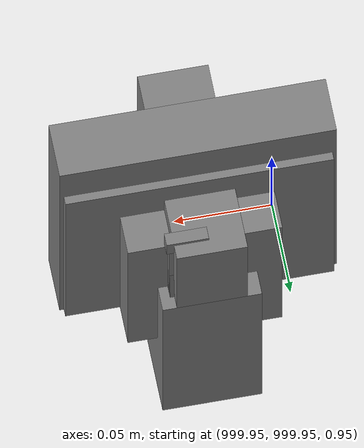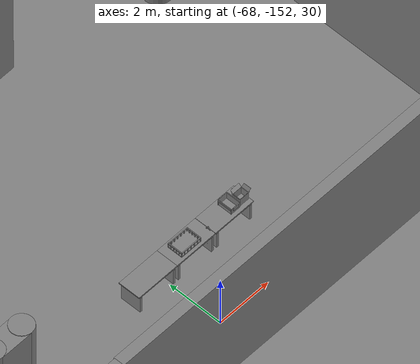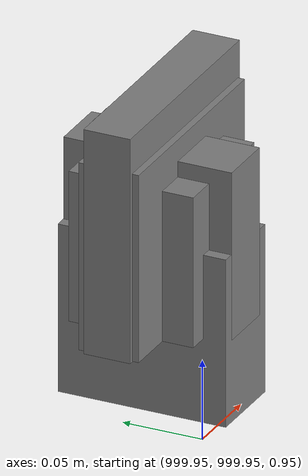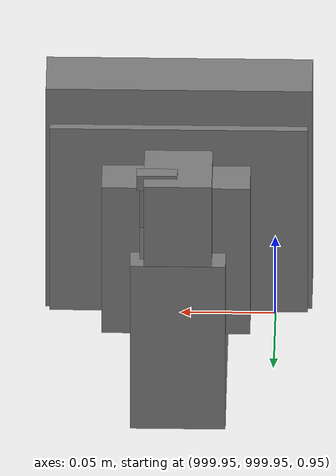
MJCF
<mujoco>
    <option gravity="0.000000000 0.000000000 -9.810000420" timestep="0.0049999999" integrator="implicitfast" density="1.225" viscosity="1.8000001e-05" noslip_iterations="10" iterations="100" sdf_iterations="50">
        <flag multiccd="disable"/>
    </option>
    <size memory="1000M"/>
    <compiler coordinate="local"/>
    <worldbody>
        <light cutoff="30" pos="0 1 1" dir="0 -1 -2"/>
        <light cutoff="30" pos="0 -1 1" dir="0 1 -2"/>
        <body pos="-65.967102051 -149.104751587 31.162647247" euler="117.977752686 31.291843414 -73.640174866" mocap="true" name="spotlight5_SpotLight"/>
        <body pos="1000.000000000 1000.000000000 1.000000000" euler="0.000000000 0.000000000 180.000000000" name="openloong_gripper_2f85_fix_base_usda_wifi_box">
            <geom contype="1" conaffinity="1" density="1000" type="box" material="" rgba="0.500000000 0.500000000 0.500000000 1.000000000" solimp="0.899999976 0.949999988 0.001000000" friction="1.000000000 0.005000000 0.000100000" solref="0.020000000 1.000000000" margin="0" condim="3" group="0" pos="0.000000000 0.000000000 0.058978677" quat="0.000000000 0.000000047 0.000000000 1.000000000" size="0.068499997 0.018999999 0.059000000" name="openloong_gripper_2f85_fix_base_usda_geom_6346B4AD_13FB_430F_8BF4_E47F4F646208"/>
            <freejoint name="openloong_gripper_2f85_fix_base_usda_wifi_box_joint"/>
            <site size="0.005000000 0.005000000 0.005000000" rgba="0.500000000 0.500000000 0.500000000 1.000000000" pos="0.000000000 0.000000000 0.000000000" quat="0.999961913 0.008726500 0.000000000 0.000000000" group="0" type="sphere" name="openloong_gripper_2f85_fix_base_usda_wifi_boxsite"/>
        </body>
        <body pos="1000.000000000 1000.000000000 1.000000000" euler="0.000000000 0.000000000 180.000000000" name="openloong_gripper_2f85_fix_base_usda_cpu_fan">
            <geom contype="1" conaffinity="1" density="1000" type="box" material="" rgba="0.500000000 0.500000000 0.500000000 1.000000000" solimp="0.899999976 0.949999988 0.001000000" friction="1.000000000 0.005000000 0.000100000" solref="0.020000000 1.000000000" margin="0" condim="3" group="0" pos="0.000000000 0.000000000 0.070034981" quat="0.000000000 0.000000000 0.000000000 1.000000000" size="0.070700005 0.014699999 0.070700005" name="openloong_gripper_2f85_fix_base_usda_geom_F96550AD_7B8D_469F_A768_C67B4A956E76"/>
            <freejoint name="openloong_gripper_2f85_fix_base_usda_cpu_fan_joint"/>
            <site size="0.005000000 0.005000000 0.005000000" rgba="0.500000000 0.500000000 0.500000000 1.000000000" pos="0.000000000 0.000000000 0.000000000" quat="0.999961913 0.008726535 0.000000000 0.000000000" group="0" type="sphere" name="openloong_gripper_2f85_fix_base_usda_cpu_fancsite"/>
        </body>
        <body pos="1000.000000000 1000.000000000 1.000000000" euler="0.000011953 0.000005123 -179.999984741" name="openloong_gripper_2f85_fix_base_usda_intel_box">
            <geom contype="1" conaffinity="1" density="1000" type="box" material="" rgba="0.500000000 0.500000000 0.500000000 1.000000000" solimp="0.899999976 0.949999988 0.001000000" friction="1.000000000 0.005000000 0.000100000" solref="0.020000000 1.000000000" margin="0" condim="3" group="0" pos="0.000000000 -0.000067139 0.000082284" quat="0.707106709 0.000000225 0.000000253 0.707106650" size="0.052800003 0.025300000 0.052800003" name="openloong_gripper_2f85_fix_base_usda_geom_FFFF5854_90B7_46FE_B1E1_E0EC10571123"/>
            <freejoint name="openloong_gripper_2f85_fix_base_usda_intel_box_joint"/>
            <site size="0.005000000 0.005000000 0.005000000" rgba="0.500000000 0.500000000 0.500000000 1.000000000" pos="0.000000000 0.000000000 0.000000000" quat="0.999961913 0.008726500 0.000000000 0.000000000" group="0" type="sphere" name="openloong_gripper_2f85_fix_base_usda_intel_boxsite"/>
        </body>
        <body pos="1000.000000000 999.999938965 1.000000000" euler="0.000000000 0.000000000 180.000000000" name="openloong_gripper_2f85_fix_base_usda_intelcore_i5">
            <geom contype="1" conaffinity="1" density="1000" type="box" material="" rgba="0.500000000 0.500000000 0.500000000 1.000000000" solimp="0.899999976 0.949999988 0.001000000" friction="1.000000000 0.005000000 0.000100000" solref="0.020000000 1.000000000" margin="0" condim="3" group="0" pos="0.000000000 0.000000000 0.051722717" quat="0.707106709 0.000000000 0.000000000 -0.707106769" size="0.052800000 0.018080002 0.052800000" name="openloong_gripper_2f85_fix_base_usda_geom_5F22DC01_F490_48CF_BB17_CA43184D7A8C"/>
            <freejoint name="openloong_gripper_2f85_fix_base_usda_intelcore_i5_joint"/>
            <site size="0.005000000 0.005000000 0.005000000" rgba="0.500000000 0.500000000 0.500000000 1.000000000" pos="0.000000000 0.000000000 0.000000000" quat="0.999961913 0.008726534 0.000000000 0.000000000" group="0" type="sphere" name="openloong_gripper_2f85_fix_base_usda_intelcore_i5site"/>
        </body>
        <body pos="-66.063491821 -148.926803589 31.169549942" euler="-112.837638855 -58.297096252 -32.915512085" mocap="true" name="spotlight2_SpotLight"/>
        <body pos="1000.000000000 1000.000000000 1.000000000" euler="0.000000000 0.000000000 180.000000000" name="openloong_gripper_2f85_fix_base_usda_battery_01">
            <geom contype="1" conaffinity="1" density="1000" type="box" material="" rgba="0.500000000 0.500000000 0.500000000 1.000000000" solimp="0.899999976 0.949999988 0.001000000" friction="1.000000000 0.005000000 0.000100000" solref="0.020000000 1.000000000" margin="0" condim="3" group="0" pos="-0.011123657 -0.041940309 0.101691343" quat="1.000000000 0.000000000 0.000000000 0.000000000" size="0.010800000 0.003375000 0.004725000" name="openloong_gripper_2f85_fix_base_usda_geom_EB8B331D_D800_45F7_9E06_0316BC6D7C76"/>
            <geom contype="1" conaffinity="1" density="1000" type="box" material="" rgba="0.500000000 0.500000000 0.500000000 1.000000000" solimp="0.899999976 0.949999988 0.001000000" friction="1.000000000 0.005000000 0.000100000" solref="0.020000000 1.000000000" margin="0" condim="3" group="0" pos="-0.010876465 -0.044247437 0.047066893" quat="0.998702705 -0.050920475 0.000000000 0.000000000" size="0.009450001 0.002700000 0.024975000" name="openloong_gripper_2f85_fix_base_usda_geom_3E5481FB_4A4B_4372_9F86_C5DB73141898"/>
            <geom contype="1" conaffinity="1" density="1000" type="box" material="" rgba="0.500000000 0.500000000 0.500000000 1.000000000" solimp="0.899999976 0.949999988 0.001000000" friction="1.000000000 0.005000000 0.000100000" solref="0.020000000 1.000000000" margin="0" condim="3" group="0" pos="-0.001235962 -0.000659180 0.047381196" quat="1.000000000 0.000000000 0.000000000 0.000000000" size="0.039420001 0.039150000 0.047250003" name="openloong_gripper_2f85_fix_base_usda_geom_6C41B0A8_AD84_4892_8642_85CCF74E48E5"/>
            <geom contype="1" conaffinity="1" density="1000" type="box" material="" rgba="0.500000000 0.500000000 0.500000000 1.000000000" solimp="0.899999976 0.949999988 0.001000000" friction="1.000000000 0.005000000 0.000100000" solref="0.020000000 1.000000000" margin="0" condim="3" group="0" pos="-0.010876465 -0.039138794 0.009851727" quat="1.000000000 0.000000000 0.000000000 0.000000000" size="0.009450001 0.010800000 0.013500000" name="openloong_gripper_2f85_fix_base_usda_geom_0B1B8E8C_FB4E_4A36_9C2D_F31068C1C9F7"/>
            <geom contype="1" conaffinity="1" density="1000" type="box" material="" rgba="0.500000000 0.500000000 0.500000000 1.000000000" solimp="0.899999976 0.949999988 0.001000000" friction="1.000000000 0.005000000 0.000100000" solref="0.020000000 1.000000000" margin="0" condim="3" group="0" pos="-0.010876465 -0.041528322 0.071508206" quat="1.000000000 0.000000000 0.000000000 0.000000000" size="0.009450001 0.002700000 0.027000001" name="openloong_gripper_2f85_fix_base_usda_geom_2813D473_0E2A_4F07_AC08_2DD0353A96F5"/>
            <freejoint name="openloong_gripper_2f85_fix_base_usda_battery_01_joint"/>
            <site size="0.005000000 0.005000000 0.005000000" rgba="0.500000000 0.500000000 0.500000000 1.000000000" pos="0.000000000 0.000000000 0.000000000" quat="0.999961913 0.008726500 0.000000000 0.000000000" group="0" type="sphere" name="openloong_gripper_2f85_fix_base_usda_battery_01site"/>
        </body>
        <body pos="-66.116027832 -149.160598755 31.170513153" euler="-100.016342163 58.317668915 8.681098938" mocap="true" name="spotlight4_SpotLight"/>
        <body pos="-64.866622925 -149.383972168 30.183746338" euler="89.999984741 89.999946594 0.000000000" name="openloong_gripper_2f85_fix_base_usda_bluebox_01">
            <geom contype="1" conaffinity="1" density="1000" type="box" material="" rgba="0.500000000 0.500000000 0.500000000 1.000000000" solimp="0.899999976 0.949999988 0.001000000" friction="1.000000000 0.005000000 0.000100000" solref="0.020000000 1.000000000" margin="0" condim="3" group="0" pos="0.276580811 0.187225342 0.000068665" quat="0.707106948 0.000077471 0.707106352 0.000077486" size="0.100000001 0.057999998 0.010000000" name="openloong_gripper_2f85_fix_base_usda_geom_8EC262C6_61FF_4071_9CF5_3513B71951D7"/>
            <geom contype="1" conaffinity="1" density="1000" type="box" material="" rgba="0.500000000 0.500000000 0.500000000 1.000000000" solimp="0.899999976 0.949999988 0.001000000" friction="1.000000000 0.005000000 0.000100000" solref="0.020000000 1.000000000" margin="0" condim="3" group="0" pos="0.000000000 0.002883911 0.000000000" quat="0.999999881 0.000000000 0.000000000 0.000000000" size="0.254000008 0.003000000 0.172000006" name="openloong_gripper_2f85_fix_base_usda_geom_5A282051_A873_443F_A992_88DA170808DA"/>
            <geom contype="1" conaffinity="1" density="1000" type="box" material="" rgba="0.500000000 0.500000000 0.500000000 1.000000000" solimp="0.899999976 0.949999988 0.001000000" friction="1.000000000 0.005000000 0.000100000" solref="0.020000000 1.000000000" margin="0" condim="3" group="0" pos="0.000000000 0.124874115 0.173484802" quat="0.999796331 0.020176515 -0.000000015 0.000000030" size="0.259999990 0.119999997 0.007000000" name="openloong_gripper_2f85_fix_base_usda_geom_198B1AB5_B73E_4C32_93F6_16C5A56D8736"/>
            <geom contype="1" conaffinity="1" density="1000" type="box" material="" rgba="0.500000000 0.500000000 0.500000000 1.000000000" solimp="0.899999976 0.949999988 0.001000000" friction="1.000000000 0.005000000 0.000100000" solref="0.020000000 1.000000000" margin="0" condim="3" group="0" pos="0.000000000 0.124874115 -0.173469543" quat="0.999796331 -0.020176545 -0.000000015 0.000000000" size="0.259999990 0.119999997 0.007000000" name="openloong_gripper_2f85_fix_base_usda_geom_ECBB7E0F_9E8F_4927_BAF9_F7D9EF28585E"/>
            <geom contype="1" conaffinity="1" density="1000" type="box" material="" rgba="0.500000000 0.500000000 0.500000000 1.000000000" solimp="0.899999976 0.949999988 0.001000000" friction="1.000000000 0.005000000 0.000100000" solref="0.020000000 1.000000000" margin="0" condim="3" group="0" pos="0.000000000 0.214008331 0.188980103" quat="0.999912977 0.013176724 0.000000015 0.000000000" size="0.259999990 0.029999999 0.012500000" name="openloong_gripper_2f85_fix_base_usda_geom_980CA626_C8B6_421D_8E9D_BB9A84D5FD57"/>
            <geom contype="1" conaffinity="1" density="1000" type="box" material="" rgba="0.500000000 0.500000000 0.500000000 1.000000000" solimp="0.899999976 0.949999988 0.001000000" friction="1.000000000 0.005000000 0.000100000" solref="0.020000000 1.000000000" margin="0" condim="3" group="0" pos="-0.258361816 0.125289917 0.001876831" quat="0.702796936 -0.020792112 0.710783124 0.020769298" size="0.189999998 0.119999997 0.009000000" name="openloong_gripper_2f85_fix_base_usda_geom_07BA267F_62CF_42CD_88F0_F4FB493EC44B"/>
            <geom contype="1" conaffinity="1" density="1000" type="box" material="" rgba="0.500000000 0.500000000 0.500000000 1.000000000" solimp="0.899999976 0.949999988 0.001000000" friction="1.000000000 0.005000000 0.000100000" solref="0.020000000 1.000000000" margin="0" condim="3" group="0" pos="0.000000000 0.214008331 -0.188980103" quat="0.999912977 -0.013176769 0.000000030 0.000000015" size="0.259999990 0.029999999 0.012500000" name="openloong_gripper_2f85_fix_base_usda_geom_C48B26D9_A69B_4644_B50C_D7D14144F762"/>
            <geom contype="1" conaffinity="1" density="1000" type="box" material="" rgba="0.500000000 0.500000000 0.500000000 1.000000000" solimp="0.899999976 0.949999988 0.001000000" friction="1.000000000 0.005000000 0.000100000" solref="0.020000000 1.000000000" margin="0" condim="3" group="0" pos="-0.276611328 0.187225342 0.000068665" quat="0.707106650 0.000077441 0.707106709 0.000077456" size="0.100000001 0.057999998 0.010000000" name="openloong_gripper_2f85_fix_base_usda_geom_2F92285D_B034_4138_86DE_8BD65A6CBC29"/>
            <geom contype="1" conaffinity="1" density="1000" type="box" material="" rgba="0.500000000 0.500000000 0.500000000 1.000000000" solimp="0.899999976 0.949999988 0.001000000" friction="1.000000000 0.005000000 0.000100000" solref="0.020000000 1.000000000" margin="0" condim="3" group="0" pos="0.258331299 0.125289917 0.001876831" quat="0.702851415 0.018856421 0.710823774 -0.019329369" size="0.189999998 0.119999997 0.009000000" name="openloong_gripper_2f85_fix_base_usda_geom_69B1FAF2_2952_4DC3_ACB3_EBCAE66E7667"/>
            <freejoint name="openloong_gripper_2f85_fix_base_usda_bluebox_01_joint"/>
            <site size="0.005000000 0.005000000 0.005000000" rgba="0.500000000 0.500000000 0.500000000 1.000000000" pos="0.000000000 0.000000000 0.000000000" quat="0.999961913 0.008726534 0.000000000 0.000000000" group="0" type="sphere" name="openloong_gripper_2f85_fix_base_usda_bluebox_01site"/>
        </body>
        <body pos="-64.496299744 -149.491867065 30.235729218" euler="0.000000000 0.000000000 89.999946594" name="openloong_gripper_2f85_fix_base_usda_cardboardbox_01">
            <geom contype="1" conaffinity="1" density="1000" type="box" material="" rgba="0.500000000 0.500000000 0.500000000 1.000000000" solimp="0.899999976 0.949999988 0.001000000" friction="1.000000000 0.005000000 0.000100000" solref="0.020000000 1.000000000" margin="0" condim="3" group="0" pos="-0.003166199 -0.004086494 0.005052090" quat="1.000000000 0.000000000 0.000000000 0.000000000" size="0.142499998 0.177500010 0.005000000" name="openloong_gripper_2f85_fix_base_usda_geom_C75186A4_485A_4566_BEE0_918B92DFF04D"/>
            <geom contype="1" conaffinity="1" density="1000" type="box" material="" rgba="0.500000000 0.500000000 0.500000000 1.000000000" solimp="0.899999976 0.949999988 0.001000000" friction="1.000000000 0.005000000 0.000100000" solref="0.020000000 1.000000000" margin="0" condim="3" group="0" pos="-0.003166199 0.170316696 0.150570869" quat="1.000000000 0.000000000 0.000000000 0.000000000" size="0.142499998 0.005000000 0.149999991" name="openloong_gripper_2f85_fix_base_usda_geom_BAE94899_5D10_4606_A58B_0BF31F07525E"/>
            <geom contype="1" conaffinity="1" density="1000" type="box" material="" rgba="0.500000000 0.500000000 0.500000000 1.000000000" solimp="0.899999976 0.949999988 0.001000000" friction="1.000000000 0.005000000 0.000100000" solref="0.020000000 1.000000000" margin="0" condim="3" group="0" pos="-0.147399902 -0.005307198 0.150570869" quat="1.000000000 0.000000000 0.000000000 0.000000000" size="0.005000000 0.177500010 0.149999991" name="openloong_gripper_2f85_fix_base_usda_geom_5C5A2EB0_3699_489E_9C8A_7A3F7605A709"/>
            <geom contype="1" conaffinity="1" density="1000" type="box" material="" rgba="0.500000000 0.500000000 0.500000000 1.000000000" solimp="0.899999976 0.949999988 0.001000000" friction="1.000000000 0.005000000 0.000100000" solref="0.020000000 1.000000000" margin="0" condim="3" group="0" pos="0.140275955 -0.005307198 0.150570869" quat="1.000000000 0.000000000 0.000000000 0.000000000" size="0.005000000 0.177500010 0.149999991" name="openloong_gripper_2f85_fix_base_usda_geom_1D838712_3CCF_40EB_8129_96131842F5E3"/>
            <geom contype="1" conaffinity="1" density="1000" type="box" material="" rgba="0.500000000 0.500000000 0.500000000 1.000000000" solimp="0.899999976 0.949999988 0.001000000" friction="1.000000000 0.005000000 0.000100000" solref="0.020000000 1.000000000" margin="0" condim="3" group="0" pos="-0.003166199 -0.181550980 0.150570869" quat="1.000000000 0.000000000 0.000000000 0.000000000" size="0.142499998 0.005000000 0.149999991" name="openloong_gripper_2f85_fix_base_usda_geom_5D87BC0B_6FB5_421C_8972_ECF6B41EB575"/>
            <freejoint name="openloong_gripper_2f85_fix_base_usda_cardboardbox_01_joint"/>
            <site size="0.005000000 0.005000000 0.005000000" rgba="0.500000000 0.500000000 0.500000000 1.000000000" pos="0.000000000 0.000000000 0.000000000" quat="0.999961913 0.008726535 0.000000000 0.000000000" group="0" type="sphere" name="openloong_gripper_2f85_fix_base_usda_site_47C3C509_C1A1_4E02_9E45_99241C8020D0"/>
            <body pos="0.139160156 -0.004048347 0.301930904" euler="-179.999954224 49.383502960 179.999954224" name="openloong_gripper_2f85_fix_base_usda_A1_006">
                <geom contype="1" conaffinity="1" density="1000" type="box" material="" rgba="0.500000000 0.500000000 0.500000000 1.000000000" solimp="0.899999976 0.949999988 0.001000000" friction="1.000000000 0.005000000 0.000100000" solref="0.020000000 1.000000000" margin="0" condim="3" group="0" pos="-0.071587563 0.000009537 0.001745224" quat="0.999999881 0.000000000 0.000000000 0.000000000" size="0.071249999 0.179999992 0.002500000" name="openloong_gripper_2f85_fix_base_usda_geom_9744D8B1_901A_42A4_B978_51151984FF14"/>
                <joint armature="0" stiffness="0.07" damping="0.0099999998" axis="0.000000 1.000000 0.000000" type="hinge" name="openloong_gripper_2f85_fix_base_usda_A1_006"/>
            </body>
            <body pos="-0.145902634 -0.004086494 0.301938057" euler="-180.000000000 -60.000011444 -180.000000000" name="openloong_gripper_2f85_fix_base_usda_A2_006">
                <geom contype="1" conaffinity="1" density="1000" type="box" material="" rgba="0.500000000 0.500000000 0.500000000 1.000000000" solimp="0.899999976 0.949999988 0.001000000" friction="1.000000000 0.005000000 0.000100000" solref="0.020000000 1.000000000" margin="0" condim="3" group="0" pos="0.071268082 0.000009537 0.002717972" quat="0.000002921 0.000000000 -0.000000030 0.999999881" size="0.071249999 0.179999992 0.002500000" name="openloong_gripper_2f85_fix_base_usda_geom_C712527F_4E04_415F_8DC8_562ADFCB6B30"/>
                <joint armature="0" stiffness="0.07" damping="0.0099999998" axis="0.000000 1.000000 0.000000" type="hinge" name="openloong_gripper_2f85_fix_base_usda_A2_006"/>
            </body>
            <body pos="-0.003385544 0.175991058 0.301930904" euler="-125.858116150 -0.000004561 0.000002331" name="openloong_gripper_2f85_fix_base_usda_B2_006">
                <geom contype="1" conaffinity="1" density="1000" type="box" material="" rgba="0.500000000 0.500000000 0.500000000 1.000000000" solimp="0.899999976 0.949999988 0.001000000" friction="1.000000000 0.005000000 0.000100000" solref="0.020000000 1.000000000" margin="0" condim="3" group="0" pos="0.000009537 -0.070939064 -0.002470016" quat="0.999614120 0.027776197 -0.000000015 0.000000030" size="0.137500003 0.064999998 0.005000000" name="openloong_gripper_2f85_fix_base_usda_geom_40A85F5A_684A_4AB9_B6DE_19C0E1B64136"/>
                <joint armature="0" stiffness="0.07" damping="0.0099999998" axis="1.000000 0.000000 0.000000" type="hinge" name="openloong_gripper_2f85_fix_base_usda_B2_006"/>
            </body>
            <body pos="-0.003385544 -0.184140205 0.301938057" euler="147.805557251 0.000000000 0.000000000" name="openloong_gripper_2f85_fix_base_usda_B1_006">
                <geom contype="1" conaffinity="1" density="1000" type="box" material="" rgba="0.500000000 0.500000000 0.500000000 1.000000000" solimp="0.899999976 0.949999988 0.001000000" friction="1.000000000 0.005000000 0.000100000" solref="0.020000000 1.000000000" margin="0" condim="3" group="0" pos="-0.000028610 0.070202351 -0.002703667" quat="0.999614179 -0.027776167 0.000000000 0.000000000" size="0.137500003 0.064999998 0.005000000" name="openloong_gripper_2f85_fix_base_usda_geom_6CD82931_76C4_4601_BF89_841DF56AD81E"/>
                <joint armature="0" stiffness="0.07" damping="0.0099999998" axis="1.000000 0.000000 0.000000" type="hinge" name="openloong_gripper_2f85_fix_base_usda_B1_006"/>
            </body>
        </body>
        <body pos="-65.882858276 -149.481979370 30.229999542" euler="-64.487716675 0.000000000 0.000000000" name="openloong_gripper_2f85_fix_base_usda_Barcode">
            <geom contype="1" conaffinity="1" density="1000" type="box" material="" rgba="0.500000000 0.500000000 0.500000000 1.000000000" solimp="0.899999976 0.949999988 0.001000000" friction="1.000000000 0.005000000 0.000100000" solref="0.020000000 1.000000000" margin="0" condim="3" group="0" pos="0.000000000 0.013038635 0.001419067" quat="0.000000000 0.000000000 0.000000000 1.000000119" size="0.034000002 0.010000000 0.017999999" name="openloong_gripper_2f85_fix_base_usda_geom_B5A12C66_56D2_421A_A907_61943743602E"/>
            <geom contype="1" conaffinity="1" density="1000" type="box" material="" rgba="0.500000000 0.500000000 0.500000000 1.000000000" solimp="0.899999976 0.949999988 0.001000000" friction="1.000000000 0.005000000 0.000100000" solref="0.020000000 1.000000000" margin="0" condim="3" group="0" pos="0.000000000 -0.035301208 -0.007095337" quat="0.000000000 0.000000000 -0.043619365 0.999048233" size="0.028999999 0.010000000 0.020000000" name="openloong_gripper_2f85_fix_base_usda_geom_07948FCD_40BE_4588_8AE4_138DBE5B78C3"/>
            <geom contype="1" conaffinity="1" density="1000" type="box" material="" rgba="0.500000000 0.500000000 0.500000000 1.000000000" solimp="0.899999976 0.949999988 0.001000000" friction="1.000000000 0.005000000 0.000100000" solref="0.020000000 1.000000000" margin="0" condim="3" group="0" pos="0.000000000 -0.043411255 -0.011749268" quat="0.922262907 0.386563420 0.000000000 0.000000000" size="0.026000001 0.010000000 0.020000000" name="openloong_gripper_2f85_fix_base_usda_geom_00A91161_58DD_4D8C_965A_C30954058FD9"/>
            <geom contype="1" conaffinity="1" density="1000" type="box" material="" rgba="0.500000000 0.500000000 0.500000000 1.000000000" solimp="0.899999976 0.949999988 0.001000000" friction="1.000000000 0.005000000 0.000100000" solref="0.020000000 1.000000000" margin="0" condim="3" group="0" pos="0.000000000 -0.016967773 -0.031860352" quat="0.000000000 0.000000000 0.000000000 1.000000119" size="0.008000000 0.010000000 0.013000000" name="openloong_gripper_2f85_fix_base_usda_geom_DFF2C643_4675_43F0_9A5C_646A964A14DF"/>
            <geom contype="1" conaffinity="1" density="1000" type="box" material="" rgba="0.500000000 0.500000000 0.500000000 1.000000000" solimp="0.899999976 0.949999988 0.001000000" friction="1.000000000 0.005000000 0.000100000" solref="0.020000000 1.000000000" margin="0" condim="3" group="0" pos="0.000000000 -0.001869202 0.000312805" quat="0.953716993 0.300705761 0.000000000 0.000000000" size="0.032000002 0.010000000 0.018999999" name="openloong_gripper_2f85_fix_base_usda_geom_F6D0F1E1_2511_4C80_B9AF_112B62B838D2"/>
            <geom contype="1" conaffinity="1" density="1000" type="box" material="" rgba="0.500000000 0.500000000 0.500000000 1.000000000" solimp="0.899999976 0.949999988 0.001000000" friction="1.000000000 0.005000000 0.000100000" solref="0.020000000 1.000000000" margin="0" condim="3" group="0" pos="0.000000000 -0.019531250 -0.003173828" quat="0.953716993 0.300705761 0.000000000 0.000000000" size="0.030999999 0.010000000 0.020000000" name="openloong_gripper_2f85_fix_base_usda_geom_17260870_511E_4392_8679_0187C87A1A34"/>
            <geom contype="1" conaffinity="1" density="1000" type="box" material="" rgba="0.500000000 0.500000000 0.500000000 1.000000000" solimp="0.899999976 0.949999988 0.001000000" friction="1.000000000 0.005000000 0.000100000" solref="0.020000000 1.000000000" margin="0" condim="3" group="0" pos="0.000000000 -0.035301208 -0.007095337" quat="0.953716993 0.300705761 0.000000000 0.000000000" size="0.028999999 0.010000000 0.020000000" name="openloong_gripper_2f85_fix_base_usda_geom_66C7DDA1_0E89_47FE_8440_7DC02917FA2B"/>
            <geom contype="1" conaffinity="1" density="1000" type="box" material="" rgba="0.500000000 0.500000000 0.500000000 1.000000000" solimp="0.899999976 0.949999988 0.001000000" friction="1.000000000 0.005000000 0.000100000" solref="0.020000000 1.000000000" margin="0" condim="3" group="0" pos="0.000000000 -0.042617798 -0.071121216" quat="0.000000000 0.000000000 0.000000000 1.000000119" size="0.013000000 0.021000000 0.059999999" name="openloong_gripper_2f85_fix_base_usda_geom_98F6548D_773C_4832_96C7_675A4676AAA8"/>
            <freejoint name="openloong_gripper_2f85_fix_base_usda_Barcode_joint"/>
            <site size="0.005000000 0.005000000 0.005000000" rgba="0.500000000 0.500000000 0.500000000 1.000000000" pos="0.000000000 0.000000000 0.000000000" quat="1.000000000 0.000000000 0.000000000 0.000000000" group="0" type="sphere" name="openloong_gripper_2f85_fix_base_usda_Barcode_site"/>
        </body>
        <body pos="-66.745018005 -149.392349243 30.184000015" euler="0.000000000 0.000000000 89.999946594" name="[22329912248516]_Basket_01">
            <geom contype="1" conaffinity="1" density="1000" type="box" material="" rgba="0.500000000 0.500000000 0.500000000 1.000000000" solimp="0.899999976 0.949999988 0.001000000" friction="1.000000000 0.005000000 0.000100000" solref="0.020000000 1.000000000" margin="0" condim="3" group="0" pos="-0.052425385 0.389207840 0.089787483" quat="0.707107008 0.000000000 0.000000000 0.707106411" size="0.014249999 0.014249999 0.059999999" name="[22329912248516]_geom_48720F97_D675_47FE_B821_5FCC2AC0BDDC"/>
            <geom contype="1" conaffinity="1" density="1000" type="box" material="" rgba="0.500000000 0.500000000 0.500000000 1.000000000" solimp="0.899999976 0.949999988 0.001000000" friction="1.000000000 0.005000000 0.000100000" solref="0.020000000 1.000000000" margin="0" condim="3" group="0" pos="0.264015198 -0.133043289 0.089787483" quat="0.707107008 0.000000000 0.000000000 0.707106411" size="0.014249999 0.014249999 0.059999999" name="[22329912248516]_geom_CD6160B1_DB41_4A35_A068_00D52A63A4A6"/>
            <geom contype="1" conaffinity="1" density="1000" type="box" material="" rgba="0.500000000 0.500000000 0.500000000 1.000000000" solimp="0.899999976 0.949999988 0.001000000" friction="1.000000000 0.005000000 0.000100000" solref="0.020000000 1.000000000" margin="0" condim="3" group="0" pos="-0.264015198 -0.265548706 0.089793205" quat="0.707107008 0.000000000 0.000000000 0.707106411" size="0.014249999 0.014249999 0.059999999" name="[22329912248516]_geom_341E9AE7_3CA4_4A76_9F3D_7479242C4347"/>
            <geom contype="1" conaffinity="1" density="1000" type="box" material="" rgba="0.500000000 0.500000000 0.500000000 1.000000000" solimp="0.899999976 0.949999988 0.001000000" friction="1.000000000 0.005000000 0.000100000" solref="0.020000000 1.000000000" margin="0" condim="3" group="0" pos="-0.160263062 -0.389322281 0.089793205" quat="0.707107008 0.000000000 0.000000000 0.707106411" size="0.014249999 0.014249999 0.059999999" name="[22329912248516]_geom_E441F456_0A5B_4730_9940_68CC2FB940F7"/>
            <geom contype="1" conaffinity="1" density="1000" type="box" material="" rgba="0.500000000 0.500000000 0.500000000 1.000000000" solimp="0.899999976 0.949999988 0.001000000" friction="1.000000000 0.005000000 0.000100000" solref="0.020000000 1.000000000" margin="0" condim="3" group="0" pos="0.162265778 -0.389322281 0.089787483" quat="0.707107008 0.000000000 0.000000000 0.707106411" size="0.014249999 0.014249999 0.059999999" name="[22329912248516]_geom_0ED0F0D7_CEA3_4165_8084_30DED5B57A68"/>
            <geom contype="1" conaffinity="1" density="1000" type="box" material="" rgba="0.500000000 0.500000000 0.500000000 1.000000000" solimp="0.899999976 0.949999988 0.001000000" friction="1.000000000 0.005000000 0.000100000" solref="0.020000000 1.000000000" margin="0" condim="3" group="0" pos="0.264015198 0.389207840 0.089787483" quat="0.707107008 0.000000000 0.000000000 0.707106411" size="0.014249999 0.014249999 0.059999999" name="[22329912248516]_geom_613DB9F6_D383_494D_89E8_C01A7DC97CFF"/>
            <geom contype="1" conaffinity="1" density="1000" type="box" material="" rgba="0.500000000 0.500000000 0.500000000 1.000000000" solimp="0.899999976 0.949999988 0.001000000" friction="1.000000000 0.005000000 0.000100000" solref="0.020000000 1.000000000" margin="0" condim="3" group="0" pos="-0.264015198 -0.133043289 0.089793205" quat="0.707107008 0.000000000 0.000000000 0.707106411" size="0.014249999 0.014249999 0.059999999" name="[22329912248516]_geom_4E0FF5DC_DDB9_4445_AB0C_400B1374EF30"/>
            <geom contype="1" conaffinity="1" density="1000" type="box" material="" rgba="0.500000000 0.500000000 0.500000000 1.000000000" solimp="0.899999976 0.949999988 0.001000000" friction="1.000000000 0.005000000 0.000100000" solref="0.020000000 1.000000000" margin="0" condim="3" group="0" pos="-0.264026642 0.269256592 0.089793205" quat="0.707107008 0.000000000 0.000000000 0.707106411" size="0.014249999 0.014249999 0.059999999" name="[22329912248516]_geom_AC22882A_9CFE_47BF_BB62_772471D39064"/>
            <geom contype="1" conaffinity="1" density="1000" type="box" material="" rgba="0.500000000 0.500000000 0.500000000 1.000000000" solimp="0.899999976 0.949999988 0.001000000" friction="1.000000000 0.005000000 0.000100000" solref="0.020000000 1.000000000" margin="0" condim="3" group="0" pos="0.054462433 0.389207840 0.089787483" quat="0.707107008 0.000000000 0.000000000 0.707106411" size="0.014249999 0.014249999 0.059999999" name="[22329912248516]_geom_40F7D09A_189A_43EE_884A_4555DA0D2462"/>
            <geom contype="1" conaffinity="1" density="1000" type="box" material="" rgba="0.500000000 0.500000000 0.500000000 1.000000000" solimp="0.899999976 0.949999988 0.001000000" friction="1.000000000 0.005000000 0.000100000" solref="0.020000000 1.000000000" margin="0" condim="3" group="0" pos="0.054462433 -0.389322281 0.089787483" quat="0.707107008 0.000000000 0.000000000 0.707106411" size="0.014249999 0.014249999 0.059999999" name="[22329912248516]_geom_15A3B01A_8033_482C_87A1_50D920AFF4D4"/>
            <geom contype="1" conaffinity="1" density="1000" type="box" material="" rgba="0.500000000 0.500000000 0.500000000 1.000000000" solimp="0.899999976 0.949999988 0.001000000" friction="1.000000000 0.005000000 0.000100000" solref="0.020000000 1.000000000" margin="0" condim="3" group="0" pos="0.264015198 0.269256592 0.089793205" quat="0.707107008 0.000000000 0.000000000 0.707106411" size="0.014249999 0.014249999 0.059999999" name="[22329912248516]_geom_445DA776_B59B_4173_84C8_D9DA2947FCF7"/>
            <geom contype="1" conaffinity="1" density="1000" type="box" material="" rgba="0.500000000 0.500000000 0.500000000 1.000000000" solimp="0.899999976 0.949999988 0.001000000" friction="1.000000000 0.005000000 0.000100000" solref="0.020000000 1.000000000" margin="0" condim="3" group="0" pos="0.264015198 -0.389322281 0.089787483" quat="0.707107008 0.000000000 0.000000000 0.707106411" size="0.014249999 0.014249999 0.059999999" name="[22329912248516]_geom_6658C6FE_76F9_46AD_8D0E_1A112290BB84"/>
            <geom contype="1" conaffinity="1" density="1000" type="box" material="" rgba="0.500000000 0.500000000 0.500000000 1.000000000" solimp="0.899999976 0.949999988 0.001000000" friction="1.000000000 0.005000000 0.000100000" solref="0.020000000 1.000000000" margin="0" condim="3" group="0" pos="0.000000000 0.000000000 0.015998840" quat="0.707107008 0.000000000 0.000000000 0.707106411" size="0.403499991 0.279000014 0.015750000" name="[22329912248516]_geom_CF9F3662_5A1C_45A0_B0CD_772542FD99D4"/>
            <geom contype="1" conaffinity="1" density="1000" type="box" material="" rgba="0.500000000 0.500000000 0.500000000 1.000000000" solimp="0.899999976 0.949999988 0.001000000" friction="1.000000000 0.005000000 0.000100000" solref="0.020000000 1.000000000" margin="0" condim="3" group="0" pos="0.000000000 -0.389476776 0.163619041" quat="0.707107008 0.000000000 0.000000000 0.707106411" size="0.015000000 0.277500004 0.015750000" name="[22329912248516]_geom_8B04D64B_D98D_49A7_93A2_4363D5F79FDD"/>
            <geom contype="1" conaffinity="1" density="1000" type="box" material="" rgba="0.500000000 0.500000000 0.500000000 1.000000000" solimp="0.899999976 0.949999988 0.001000000" friction="1.000000000 0.005000000 0.000100000" solref="0.020000000 1.000000000" margin="0" condim="3" group="0" pos="0.162265778 0.389207840 0.089787483" quat="0.707107008 0.000000000 0.000000000 0.707106411" size="0.014249999 0.014249999 0.059999999" name="[22329912248516]_geom_B3D80696_0825_46A5_AC46_15DC87048955"/>
            <geom contype="1" conaffinity="1" density="1000" type="box" material="" rgba="0.500000000 0.500000000 0.500000000 1.000000000" solimp="0.899999976 0.949999988 0.001000000" friction="1.000000000 0.005000000 0.000100000" solref="0.020000000 1.000000000" margin="0" condim="3" group="0" pos="0.000000000 0.389471054 0.163619041" quat="0.707107008 0.000000000 0.000000000 0.707106411" size="0.015000000 0.277500004 0.015750000" name="[22329912248516]_geom_CF81FAA2_7EE6_4A88_8D9B_855A1AF64076"/>
            <geom contype="1" conaffinity="1" density="1000" type="box" material="" rgba="0.500000000 0.500000000 0.500000000 1.000000000" solimp="0.899999976 0.949999988 0.001000000" friction="1.000000000 0.005000000 0.000100000" solref="0.020000000 1.000000000" margin="0" condim="3" group="0" pos="-0.263511658 0.000000000 0.163619041" quat="0.707107008 0.000000000 0.000000000 0.707106411" size="0.403499991 0.015000000 0.015750000" name="[22329912248516]_geom_EE1DA165_B838_4099_A4A8_C41FACAFB062"/>
            <geom contype="1" conaffinity="1" density="1000" type="box" material="" rgba="0.500000000 0.500000000 0.500000000 1.000000000" solimp="0.899999976 0.949999988 0.001000000" friction="1.000000000 0.005000000 0.000100000" solref="0.020000000 1.000000000" margin="0" condim="3" group="0" pos="-0.264015198 0.141334534 0.089793205" quat="0.707107008 0.000000000 0.000000000 0.707106411" size="0.014249999 0.014249999 0.059999999" name="[22329912248516]_geom_0B004588_9A5A_47AE_A923_43D77465175A"/>
            <geom contype="1" conaffinity="1" density="1000" type="box" material="" rgba="0.500000000 0.500000000 0.500000000 1.000000000" solimp="0.899999976 0.949999988 0.001000000" friction="1.000000000 0.005000000 0.000100000" solref="0.020000000 1.000000000" margin="0" condim="3" group="0" pos="0.264015198 -0.265548706 0.089787483" quat="0.707107008 0.000000000 0.000000000 0.707106411" size="0.014249999 0.014249999 0.059999999" name="[22329912248516]_geom_92B2EB28_C5B9_42CE_96E3_6A26D6D87446"/>
            <geom contype="1" conaffinity="1" density="1000" type="box" material="" rgba="0.500000000 0.500000000 0.500000000 1.000000000" solimp="0.899999976 0.949999988 0.001000000" friction="1.000000000 0.005000000 0.000100000" solref="0.020000000 1.000000000" margin="0" condim="3" group="0" pos="-0.160263062 0.389207840 0.089787483" quat="0.707107008 0.000000000 0.000000000 0.707106411" size="0.014249999 0.014249999 0.059999999" name="[22329912248516]_geom_ACE1263D_55A0_4E78_AAD6_D2CE585555BD"/>
            <geom contype="1" conaffinity="1" density="1000" type="box" material="" rgba="0.500000000 0.500000000 0.500000000 1.000000000" solimp="0.899999976 0.949999988 0.001000000" friction="1.000000000 0.005000000 0.000100000" solref="0.020000000 1.000000000" margin="0" condim="3" group="0" pos="-0.052425385 -0.389322281 0.089787483" quat="0.707107008 0.000000000 0.000000000 0.707106411" size="0.014249999 0.014249999 0.059999999" name="[22329912248516]_geom_2C8173BE_EF47_48E5_A9CE_F950FC89C7AB"/>
            <geom contype="1" conaffinity="1" density="1000" type="box" material="" rgba="0.500000000 0.500000000 0.500000000 1.000000000" solimp="0.899999976 0.949999988 0.001000000" friction="1.000000000 0.005000000 0.000100000" solref="0.020000000 1.000000000" margin="0" condim="3" group="0" pos="-0.264026642 -0.389322281 0.089793205" quat="0.707107008 0.000000000 0.000000000 0.707106411" size="0.014249999 0.014249999 0.059999999" name="[22329912248516]_geom_59C33CC7_42A1_4CED_AD4F_AE716F36E89F"/>
            <geom contype="1" conaffinity="1" density="1000" type="box" material="" rgba="0.500000000 0.500000000 0.500000000 1.000000000" solimp="0.899999976 0.949999988 0.001000000" friction="1.000000000 0.005000000 0.000100000" solref="0.020000000 1.000000000" margin="0" condim="3" group="0" pos="0.264015198 0.141334534 0.089787483" quat="0.707107008 0.000000000 0.000000000 0.707106411" size="0.014249999 0.014249999 0.059999999" name="[22329912248516]_geom_D868649D_8051_43B9_9B58_F9DEFC339F8F"/>
            <geom contype="1" conaffinity="1" density="1000" type="box" material="" rgba="0.500000000 0.500000000 0.500000000 1.000000000" solimp="0.899999976 0.949999988 0.001000000" friction="1.000000000 0.005000000 0.000100000" solref="0.020000000 1.000000000" margin="0" condim="3" group="0" pos="-0.264015198 0.389207840 0.089793205" quat="0.707107008 0.000000000 0.000000000 0.707106411" size="0.014249999 0.014249999 0.059999999" name="[22329912248516]_geom_46F64C2E_224C_481A_9F50_2ED0DC119A89"/>
            <geom contype="1" conaffinity="1" density="1000" type="box" material="" rgba="0.500000000 0.500000000 0.500000000 1.000000000" solimp="0.899999976 0.949999988 0.001000000" friction="1.000000000 0.005000000 0.000100000" solref="0.020000000 1.000000000" margin="0" condim="3" group="0" pos="0.264015198 0.004480362 0.089787483" quat="0.707107008 0.000000000 0.000000000 0.707106411" size="0.014249999 0.014249999 0.059999999" name="[22329912248516]_geom_E030F4D6_6E96_4167_9B0B_97A7D10ED31E"/>
            <geom contype="1" conaffinity="1" density="1000" type="box" material="" rgba="0.500000000 0.500000000 0.500000000 1.000000000" solimp="0.899999976 0.949999988 0.001000000" friction="1.000000000 0.005000000 0.000100000" solref="0.020000000 1.000000000" margin="0" condim="3" group="0" pos="0.263694763 -0.000011444 0.163619041" quat="0.707107008 0.000000000 0.000000000 0.707106411" size="0.403499991 0.015000000 0.015750000" name="[22329912248516]_geom_526BA4A1_E2CE_46C9_947F_F53FD404A3C4"/>
            <geom contype="1" conaffinity="1" density="1000" type="box" material="" rgba="0.500000000 0.500000000 0.500000000 1.000000000" solimp="0.899999976 0.949999988 0.001000000" friction="1.000000000 0.005000000 0.000100000" solref="0.020000000 1.000000000" margin="0" condim="3" group="0" pos="-0.264015198 0.004480362 0.089793205" quat="0.707107008 0.000000000 0.000000000 0.707106411" size="0.014249999 0.014249999 0.059999999" name="[22329912248516]_geom_6C895C06_8A13_49AC_93C1_53182125339A"/>
            <freejoint name="[22329912248516]_joint_DC203B04_CCE0_4586_BAF2_F114B19D6626"/>
        </body>
        <body pos="0.000000000 0.000000000 0.000000000" euler="0.000000000 0.000000000 0.000000000" name="Static Objects_Static Objects">
            <geom contype="1" conaffinity="1" density="1000" type="box" material="" rgba="0.500000000 0.500000000 0.500000000 1.000000000" solimp="0.899999976 0.949999988 0.001000000" friction="1.000000000 0.005000000 0.000100000" solref="0.020000000 1.000000000" margin="0" condim="3" group="0" pos="-67.544113159 -149.365814209 29.727830887" quat="0.500000417 0.499999970 0.499999553 0.499999970" size="0.381000012 0.319999993 0.041000001" name="Static Objects_geom_EDCD89DB_0995_421A_B52C_60E7A06556C0"/>
            <geom contype="1" conaffinity="1" density="1000" type="box" material="" rgba="0.500000000 0.500000000 0.500000000 1.000000000" solimp="0.899999976 0.949999988 0.001000000" friction="1.000000000 0.005000000 0.000100000" solref="0.020000000 1.000000000" margin="0" condim="3" group="0" pos="-68.239501953 -149.365814209 30.086868286" quat="0.500000417 0.499999970 0.499999553 0.499999970" size="0.370999992 0.039500002 0.745000005" name="Static Objects_geom_0A3EC87A_4355_4762_AA05_E5FF6A4F144B"/>
            <geom contype="1" conaffinity="1" density="1000" type="box" material="" rgba="0.500000000 0.500000000 0.500000000 1.000000000" solimp="0.899999976 0.949999988 0.001000000" friction="1.000000000 0.005000000 0.000100000" solref="0.020000000 1.000000000" margin="0" condim="3" group="0" pos="-68.239501953 -149.365814209 30.147235870" quat="0.500000417 0.499999970 0.499999553 0.499999970" size="0.400000006 0.022000000 0.800000012" name="Static Objects_geom_51A13F8D_8CDE_41F1_9B78_0D547A2AADB5"/>
            <geom contype="1" conaffinity="1" density="1000" type="box" material="" rgba="0.500000000 0.500000000 0.500000000 1.000000000" solimp="0.899999976 0.949999988 0.001000000" friction="1.000000000 0.005000000 0.000100000" solref="0.020000000 1.000000000" margin="0" condim="3" group="0" pos="-68.934890747 -149.365814209 29.727830887" quat="0.500000417 0.499999970 0.499999553 0.499999970" size="0.381000012 0.319999993 0.041000001" name="Static Objects_geom_8CB22340_4A16_43A0_8CF8_20C05D904CD8"/>
            <geom contype="1" conaffinity="1" density="1000" type="box" material="" rgba="0.500000000 0.500000000 0.500000000 1.000000000" solimp="0.899999976 0.949999988 0.001000000" friction="1.000000000 0.005000000 0.000100000" solref="0.020000000 1.000000000" margin="0" condim="3" group="0" pos="-68.239501953 -149.365814209 29.561563492" quat="0.500000417 0.499999970 0.499999553 0.499999970" size="0.020000000 0.022000000 0.660000026" name="Static Objects_geom_BC963FED_9440_4854_92D5_5C1A9753DBAC"/>
            <geom contype="1" conaffinity="1" density="1000" type="box" material="" rgba="0.500000000 0.500000000 0.500000000 1.000000000" solimp="0.899999976 0.949999988 0.001000000" friction="1.000000000 0.005000000 0.000100000" solref="0.020000000 1.000000000" margin="0" condim="3" group="0" pos="-65.945671082 -149.365814209 29.727830887" quat="0.500000417 0.499999970 0.499999553 0.499999970" size="0.381000012 0.319999993 0.041000001" name="Static Objects_geom_F1522064_986C_4B46_9E89_3AA411056291"/>
            <geom contype="1" conaffinity="1" density="1000" type="box" material="" rgba="0.500000000 0.500000000 0.500000000 1.000000000" solimp="0.899999976 0.949999988 0.001000000" friction="1.000000000 0.005000000 0.000100000" solref="0.020000000 1.000000000" margin="0" condim="3" group="0" pos="-66.641059875 -149.365814209 30.086868286" quat="0.500000417 0.499999970 0.499999553 0.499999970" size="0.370999992 0.039500002 0.745000005" name="Static Objects_geom_2FAFFE41_05AA_475A_A087_66A47D23FAB9"/>
            <geom contype="1" conaffinity="1" density="1000" type="box" material="" rgba="0.500000000 0.500000000 0.500000000 1.000000000" solimp="0.899999976 0.949999988 0.001000000" friction="1.000000000 0.005000000 0.000100000" solref="0.020000000 1.000000000" margin="0" condim="3" group="0" pos="-66.641059875 -149.365814209 30.147235870" quat="0.500000417 0.499999970 0.499999553 0.499999970" size="0.400000006 0.022000000 0.800000012" name="Static Objects_geom_5A5D773C_7080_47FF_B8E6_616A7795A936"/>
            <geom contype="1" conaffinity="1" density="1000" type="box" material="" rgba="0.500000000 0.500000000 0.500000000 1.000000000" solimp="0.899999976 0.949999988 0.001000000" friction="1.000000000 0.005000000 0.000100000" solref="0.020000000 1.000000000" margin="0" condim="3" group="0" pos="-67.336448669 -149.365814209 29.727830887" quat="0.500000417 0.499999970 0.499999553 0.499999970" size="0.381000012 0.319999993 0.041000001" name="Static Objects_geom_4A10102B_F8B0_44D9_A7FC_9CD9AE9210AF"/>
            <geom contype="1" conaffinity="1" density="1000" type="box" material="" rgba="0.500000000 0.500000000 0.500000000 1.000000000" solimp="0.899999976 0.949999988 0.001000000" friction="1.000000000 0.005000000 0.000100000" solref="0.020000000 1.000000000" margin="0" condim="3" group="0" pos="-66.641059875 -149.365814209 29.561563492" quat="0.500000417 0.499999970 0.499999553 0.499999970" size="0.020000000 0.022000000 0.660000026" name="Static Objects_geom_7B1E107E_37F7_43FA_898D_BF856147F777"/>
            <geom contype="1" conaffinity="1" density="1000" type="box" material="" rgba="0.500000000 0.500000000 0.500000000 1.000000000" solimp="0.899999976 0.949999988 0.001000000" friction="1.000000000 0.005000000 0.000100000" solref="0.020000000 1.000000000" margin="0" condim="3" group="0" pos="-64.338577271 -149.365814209 29.727830887" quat="0.500000417 0.499999970 0.499999553 0.499999970" size="0.381000012 0.319999993 0.041000001" name="Static Objects_geom_CD930483_9B0D_4391_89A7_0365FC872716"/>
            <geom contype="1" conaffinity="1" density="1000" type="box" material="" rgba="0.500000000 0.500000000 0.500000000 1.000000000" solimp="0.899999976 0.949999988 0.001000000" friction="1.000000000 0.005000000 0.000100000" solref="0.020000000 1.000000000" margin="0" condim="3" group="0" pos="-65.033966064 -149.365814209 30.086868286" quat="0.500000417 0.499999970 0.499999553 0.499999970" size="0.370999992 0.039500002 0.745000005" name="Static Objects_geom_0A6D42F2_8C4D_4D51_82E5_27989D78BF39"/>
            <geom contype="1" conaffinity="1" density="1000" type="box" material="" rgba="0.500000000 0.500000000 0.500000000 1.000000000" solimp="0.899999976 0.949999988 0.001000000" friction="1.000000000 0.005000000 0.000100000" solref="0.020000000 1.000000000" margin="0" condim="3" group="0" pos="-65.033966064 -149.365814209 30.147235870" quat="0.500000417 0.499999970 0.499999553 0.499999970" size="0.400000006 0.022000000 0.800000012" name="Static Objects_geom_442258F2_E10D_4CFF_A341_CE90CDAAE057"/>
            <geom contype="1" conaffinity="1" density="1000" type="box" material="" rgba="0.500000000 0.500000000 0.500000000 1.000000000" solimp="0.899999976 0.949999988 0.001000000" friction="1.000000000 0.005000000 0.000100000" solref="0.020000000 1.000000000" margin="0" condim="3" group="0" pos="-65.729354858 -149.365814209 29.727830887" quat="0.500000417 0.499999970 0.499999553 0.499999970" size="0.381000012 0.319999993 0.041000001" name="Static Objects_geom_FD5E90C2_FC3A_4968_8C3A_025EC11A344A"/>
            <geom contype="1" conaffinity="1" density="1000" type="box" material="" rgba="0.500000000 0.500000000 0.500000000 1.000000000" solimp="0.899999976 0.949999988 0.001000000" friction="1.000000000 0.005000000 0.000100000" solref="0.020000000 1.000000000" margin="0" condim="3" group="0" pos="-65.033966064 -149.365814209 29.561563492" quat="0.500000417 0.499999970 0.499999553 0.499999970" size="0.020000000 0.022000000 0.660000026" name="Static Objects_geom_014D8B62_0D56_4AD4_BC67_2E65F90DEB4A"/>
            <geom contype="1" conaffinity="1" density="1000" type="box" material="" rgba="0.500000000 0.500000000 0.500000000 1.000000000" solimp="0.899999976 0.949999988 0.001000000" friction="1.000000000 0.005000000 0.000100000" solref="0.020000000 1.000000000" margin="0" condim="3" group="0" pos="-61.754566193 -137.853729248 33.906845093" quat="0.707107067 0.000000000 0.000000000 0.707106471" size="0.759999990 0.759999990 4.500000000" name="Static Objects_geom_D3A7AA30_C486_409C_ACC8_7C5F06393EE6"/>
            <geom contype="1" conaffinity="1" density="1000" type="box" material="" rgba="0.500000000 0.500000000 0.500000000 1.000000000" solimp="0.899999976 0.949999988 0.001000000" friction="1.000000000 0.005000000 0.000100000" solref="0.020000000 1.000000000" margin="0" condim="3" group="0" pos="-57.511135101 -144.927108765 31.707921982" quat="1.000000000 0.000000000 0.000000000 0.000000000" size="0.200000003 8.000000000 2.299999952" name="Static Objects_geom_E743124B_0205_4661_B697_A89284B70B79"/>
            <geom contype="1" conaffinity="1" density="1000" type="box" material="" rgba="0.500000000 0.500000000 0.500000000 1.000000000" solimp="0.899999976 0.949999988 0.001000000" friction="1.000000000 0.005000000 0.000100000" solref="0.020000000 1.000000000" margin="0" condim="3" group="0" pos="-80.517646790 -157.574050903 31.688196182" quat="0.707107067 0.000000000 0.000000000 0.707106471" size="0.600000024 0.600000024 2.299999952" name="Static Objects_geom_9039C45A_16C7_4828_91EC_24D5465F5808"/>
            <geom contype="1" conaffinity="1" density="1000" type="box" material="" rgba="0.500000000 0.500000000 0.500000000 1.000000000" solimp="0.899999976 0.949999988 0.001000000" friction="1.000000000 0.005000000 0.000100000" solref="0.020000000 1.000000000" margin="0" condim="3" group="0" pos="-80.711044312 -147.414932251 31.666158676" quat="1.000000000 0.000000000 0.000000000 0.000000000" size="0.200000003 10.000000000 2.299999952" name="Static Objects_geom_10B2B314_0313_4F80_9579_AAD79C370672"/>
            <geom contype="1" conaffinity="1" density="1000" type="box" material="" rgba="0.500000000 0.500000000 0.500000000 1.000000000" solimp="0.899999976 0.949999988 0.001000000" friction="1.000000000 0.005000000 0.000100000" solref="0.020000000 1.000000000" margin="0" condim="3" group="0" pos="-57.687217712 -137.434692383 31.688196182" quat="0.707107067 0.000000000 0.000000000 0.707106471" size="0.600000024 0.600000024 2.299999952" name="Static Objects_geom_DC4C9CCA_CB45_4195_AF83_EFE1EEC1F7CA"/>
            <geom contype="1" conaffinity="1" density="1000" type="box" material="" rgba="0.500000000 0.500000000 0.500000000 1.000000000" solimp="0.899999976 0.949999988 0.001000000" friction="1.000000000 0.005000000 0.000100000" solref="0.020000000 1.000000000" margin="0" condim="3" group="0" pos="-69.537033081 -140.263229370 31.714921951" quat="0.707107067 0.000000000 0.000000000 0.707106471" size="0.759999990 4.500000000 2.299999952" name="Static Objects_geom_BBD92DC8_BAC7_4CA0_84AF_29B3887E228A"/>
            <geom contype="1" conaffinity="1" density="1000" type="box" material="" rgba="0.500000000 0.500000000 0.500000000 1.000000000" solimp="0.899999976 0.949999988 0.001000000" friction="1.000000000 0.005000000 0.000100000" solref="0.020000000 1.000000000" margin="0" condim="3" group="0" pos="-80.073638916 -137.853713989 33.906845093" quat="0.707107067 0.000000000 0.000000000 0.707106471" size="0.759999990 0.759999990 4.500000000" name="Static Objects_geom_7DC38F9F_DDC2_4530_B3AD_16FC58E0C408"/>
            <geom contype="1" conaffinity="1" density="1000" type="box" material="" rgba="0.500000000 0.500000000 0.500000000 1.000000000" solimp="0.899999976 0.949999988 0.001000000" friction="1.000000000 0.005000000 0.000100000" solref="0.020000000 1.000000000" margin="0" condim="3" group="0" pos="-73.406707764 -155.734664917 31.707921982" quat="1.000000000 0.000000000 0.000000000 0.000000000" size="0.200000003 3.000000000 2.299999952" name="Static Objects_geom_2D76E309_5315_45EE_9C65_AE63FE208BBE"/>
            <geom contype="1" conaffinity="1" density="1000" type="box" material="" rgba="0.500000000 0.500000000 0.500000000 1.000000000" solimp="0.899999976 0.949999988 0.001000000" friction="1.000000000 0.005000000 0.000100000" solref="0.020000000 1.000000000" margin="0" condim="3" group="0" pos="-68.497543335 -137.448257446 31.707921982" quat="0.707107067 0.000000000 0.000000000 0.707106471" size="0.200000003 14.000000000 2.299999952" name="Static Objects_geom_18F7C7CE_8EF2_4FA3_9841_5952990BE05C"/>
            <geom contype="1" conaffinity="1" density="1000" type="cylinder" material="" rgba="0.500000000 0.500000000 0.500000000 1.000000000" solimp="0.899999976 0.949999988 0.001000000" friction="1.000000000 0.005000000 0.000100000" solref="0.020000000 1.000000000" margin="0" condim="3" group="0" pos="-68.868522644 -142.134506226 31.711090088" quat="0.707107067 0.000000000 0.000000000 0.707106471" size="0.509999990 2.299999952 1.000000000" name="Static Objects_geom_7D3D8528_CE55_42DA_B4A0_6E4BC1855131"/>
            <geom contype="1" conaffinity="1" density="1000" type="plane" material="" rgba="0.500000000 0.500000000 0.500000000 1.000000000" solimp="0.899999976 0.949999988 0.001000000" friction="1.000000000 0.005000000 0.000100000" solref="0.020000000 1.000000000" margin="0" condim="3" group="0" pos="-72.873703003 -147.131927490 29.409669876" quat="1.000000000 0.000000000 0.000000000 0.000000000" size="18.000000000 14.000000000 1.000000000" name="Static Objects_geom_1FB678F3_73BB_46B2_90C6_74CBFDB1E53B"/>
            <geom contype="1" conaffinity="1" density="1000" type="box" material="" rgba="0.500000000 0.500000000 0.500000000 1.000000000" solimp="0.899999976 0.949999988 0.001000000" friction="1.000000000 0.005000000 0.000100000" solref="0.020000000 1.000000000" margin="0" condim="3" group="0" pos="-79.943580627 -157.782272339 31.707921982" quat="0.707107067 0.000000000 0.000000000 0.707106471" size="0.200000003 7.000000000 2.299999952" name="Static Objects_geom_D6E137C7_FE7C_431D_9AEA_D947E3A51C7A"/>
            <geom contype="1" conaffinity="1" density="1000" type="box" material="" rgba="0.500000000 0.500000000 0.500000000 1.000000000" solimp="0.899999976 0.949999988 0.001000000" friction="1.000000000 0.005000000 0.000100000" solref="0.020000000 1.000000000" margin="0" condim="3" group="0" pos="-65.421028137 -152.903442383 31.707921982" quat="0.707107067 0.000000000 0.000000000 0.707106471" size="0.200000003 7.800000191 2.299999952" name="Static Objects_geom_5AB9EB9C_C9A2_493E_A0E5_FA55FB57FF6F"/>
            <geom contype="1" conaffinity="1" density="1000" type="box" material="" rgba="0.500000000 0.500000000 0.500000000 1.000000000" solimp="0.899999976 0.949999988 0.001000000" friction="1.000000000 0.005000000 0.000100000" solref="0.020000000 1.000000000" margin="0" condim="3" group="0" pos="-74.776908875 -149.964416504 31.688196182" quat="1.000000000 0.000000000 0.000000000 0.000000000" size="0.600000024 0.409999996 2.299999952" name="Static Objects_geom_9DFF9DCB_A51B_4F3E_A575_985E9BDE7749"/>
            <geom contype="1" conaffinity="1" density="1000" type="cylinder" material="" rgba="0.500000000 0.500000000 0.500000000 1.000000000" solimp="0.899999976 0.949999988 0.001000000" friction="1.000000000 0.005000000 0.000100000" solref="0.020000000 1.000000000" margin="0" condim="3" group="0" pos="-60.161884308 -142.134506226 31.711090088" quat="0.707107067 0.000000000 0.000000000 0.707106471" size="0.509999990 2.299999952 1.000000000" name="Static Objects_geom_1A2D2F66_C052_44B7_AC84_E2DA509037A2"/>
            <geom contype="1" conaffinity="1" density="1000" type="cylinder" material="" rgba="0.500000000 0.500000000 0.500000000 1.000000000" solimp="0.899999976 0.949999988 0.001000000" friction="1.000000000 0.005000000 0.000100000" solref="0.020000000 1.000000000" margin="0" condim="3" group="0" pos="-75.382453918 -149.963455200 31.711090088" quat="0.707107067 0.000000000 0.000000000 0.707106471" size="0.409999996 2.299999952 1.000000000" name="Static Objects_geom_DC965D61_760B_4120_A6B9_F8F27E49D8E5"/>
            <geom contype="1" conaffinity="1" density="1000" type="cylinder" material="" rgba="0.500000000 0.500000000 0.500000000 1.000000000" solimp="0.899999976 0.949999988 0.001000000" friction="1.000000000 0.005000000 0.000100000" solref="0.020000000 1.000000000" margin="0" condim="3" group="0" pos="-74.154960632 -149.963455200 31.711090088" quat="0.707107067 0.000000000 0.000000000 0.707106471" size="0.409999996 2.299999952 1.000000000" name="Static Objects_geom_6A87239E_0193_4197_B834_F62A801E19CF"/>
            <geom contype="1" conaffinity="1" density="1000" type="cylinder" material="" rgba="0.500000000 0.500000000 0.500000000 1.000000000" solimp="0.899999976 0.949999988 0.001000000" friction="1.000000000 0.005000000 0.000100000" solref="0.020000000 1.000000000" margin="0" condim="3" group="0" pos="-77.566612244 -142.134506226 31.711090088" quat="0.707107067 0.000000000 0.000000000 0.707106471" size="0.509999990 2.299999952 1.000000000" name="Static Objects_geom_33C5D7A1_3EA9_4C91_BBE1_FB673248A9B6"/>
        </body>
        <body pos="-66.291030884 -149.869689941 29.018842697" euler="0.000000000 0.000000000 89.999946594" mocap="true" name="openloong_gripper_2f85_fix_base_usda_leftHandMocap"/>
        <body pos="-66.291030884 -149.869689941 29.018842697" euler="0.000000000 0.000000000 89.999946594" mocap="true" name="openloong_gripper_2f85_fix_base_usda_rightHandMocap"/>
        <body pos="-66.291030884 -149.869689941 30.218843460" euler="0.000000000 0.000000000 89.999946594" name="openloong_gripper_2f85_fix_base_usda_base_link">
            <geom contype="1" conaffinity="1" density="1000" type="mesh" material="" rgba="0.783999979 0.783999979 0.783999979 1.000000000" solimp="0.899999976 0.949999988 0.001000000" friction="1.000000000 0.005000000 0.000100000" solref="0.020000000 1.000000000" margin="0" condim="3" group="3" mesh="base_link" pos="0.000000000 0.000000000 0.000000000" quat="1.000000000 0.000000000 0.000000000 0.000000000" size="1.000000000 1.000000000 1.000000000" name="openloong_gripper_2f85_fix_base_usda__geom_7_02045A12_63F9_4EB4_B1D7_7ACD2358BFBF"/>
            <site size="0.005000000 0.005000000 0.005000000" rgba="0.500000000 0.500000000 0.500000000 1.000000000" pos="0.000000000 0.000000000 0.000000000" quat="1.000000000 0.000000000 0.000000000 0.000000000" group="0" type="sphere" name="openloong_gripper_2f85_fix_base_usda_imu"/>
            <inertial mass="22.447001" pos="-0.005664100 -0.001336700 0.238289997" diaginertia="0.374352545 0.277180195 0.220617250" quat="0.999247074 0.035235517 -0.015086859 0.006023135"/>
            <body pos="0.000000000 0.000000000 0.299997330" euler="0.000000000 0.000000000 0.000000000" name="openloong_gripper_2f85_fix_base_usda_dummy_body">
                <geom contype="1" conaffinity="1" density="1000" type="sphere" material="" rgba="0.783999979 0.783999979 0.783999979 1.000000000" solimp="0.899999976 0.949999988 0.001000000" friction="1.000000000 0.005000000 0.000100000" solref="0.020000000 1.000000000" margin="0" condim="3" group="3" pos="0.000000000 0.000000000 0.000000000" quat="1.000000000 0.000000000 0.000000000 0.000000000" size="0.010000000 0.000000000 0.000000000" name="openloong_gripper_2f85_fix_base_usda__geom_8_8A2F0FC7_24C6_4ECB_9591_5A1149997372"/>
                <joint armature="0.0099999998" stiffness="0" damping="0.1" axis="0.000000 0.000000 1.000000" type="hinge" name="openloong_gripper_2f85_fix_base_usda_dummy_joint"/>
                <site size="0.010000000 0.005000000 0.005000000" rgba="0.500000000 0.500000000 0.500000000 1.000000000" pos="0.000000000 0.000000000 0.000000000" quat="1.000000000 0.000000000 0.000000000 0.000000000" group="3" type="sphere" name="openloong_gripper_2f85_fix_base_usda_dummy_site"/>
            </body>
            <body pos="0.009002686 0.000000000 0.406400681" euler="0.000000000 0.000000000 0.000000000" name="openloong_gripper_2f85_fix_base_usda_Link_head_yaw">
                <geom contype="1" conaffinity="1" density="1000" type="mesh" material="" rgba="0.783999979 0.783999979 0.783999979 1.000000000" solimp="0.899999976 0.949999988 0.001000000" friction="1.000000000 0.005000000 0.000100000" solref="0.020000000 1.000000000" margin="0" condim="3" group="3" mesh="Link_head_yaw" pos="0.000000000 0.000000000 0.000000000" quat="1.000000000 0.000000000 0.000000000 0.000000000" size="1.000000000 1.000000000 1.000000000" name="openloong_gripper_2f85_fix_base_usda__geom_10_E6D15CCE_8AA2_4E7A_BC7F_A43792BAC047"/>
                <inertial mass="0.84249002" pos="0.000000000 -0.002081400 0.044801001" diaginertia="0.000700588 0.000629000 0.000553812" quat="0.706933022 -0.015675601 0.015677100 0.706933022"/>
                <body pos="0.000000000 -0.034599304 0.048500061" euler="0.000000000 0.000000000 0.000000000" name="openloong_gripper_2f85_fix_base_usda_Link_head_pitch">
                    <geom contype="1" conaffinity="1" density="1000" type="mesh" material="" rgba="0.783999979 0.783999979 0.783999979 1.000000000" solimp="0.899999976 0.949999988 0.001000000" friction="1.000000000 0.005000000 0.000100000" solref="0.020000000 1.000000000" margin="0" condim="3" group="3" mesh="Link_head_pitch" pos="0.000000000 0.000000000 0.000000000" quat="1.000000000 0.000000000 0.000000000 0.000000000" size="1.000000000 1.000000000 1.000000000" name="openloong_gripper_2f85_fix_base_usda__geom_12_7B6AFBA4_546A_4C9C_B79C_AF4C3C64BE3D"/>
                    <inertial mass="1.3943" pos="0.020569000 0.033004001 0.125000000" diaginertia="0.006381400 0.006289940 0.004481460" quat="0.973390222 0.008406822 0.228157058 0.019624906"/>
                    <body pos="0.000000000 0.029998779 0.000000000" euler="0.000000000 0.000000000 0.000000000" name="openloong_gripper_2f85_fix_base_usda_neck_center_body">
                        <site size="0.010000000 0.005000000 0.005000000" rgba="0.500000000 0.500000000 0.500000000 1.000000000" pos="0.000000000 0.000000000 0.000000000" quat="1.000000000 0.000000000 0.000000000 0.000000000" group="3" type="sphere" name="openloong_gripper_2f85_fix_base_usda_neck_center_site"/>
                        <body pos="0.020004272 0.000000000 0.149999619" euler="-0.000002229 39.998176575 -90.000205994" name="openloong_gripper_2f85_fix_base_usda_camera_head">
                            <site size="0.010000000 0.005000000 0.005000000" rgba="0.500000000 0.500000000 0.500000000 1.000000000" pos="0.000000000 0.000000000 0.000000000" quat="1.000000000 0.000000000 0.000000000 0.000000000" group="3" type="sphere" name="openloong_gripper_2f85_fix_base_usda_camera_head_site"/>
                        </body>
                    </body>
                </body>
            </body>
            <body pos="0.003997803 -0.161598206 0.392200470" euler="0.000000000 0.000000000 0.000000000" name="openloong_gripper_2f85_fix_base_usda_Link_arm_r_01">
                <geom contype="1" conaffinity="1" density="1000" type="mesh" material="" rgba="0.783999979 0.783999979 0.783999979 1.000000000" solimp="0.899999976 0.949999988 0.001000000" friction="1.000000000 0.005000000 0.000100000" solref="0.020000000 1.000000000" margin="0" condim="3" group="3" mesh="Link_arm_r_01" pos="0.000000000 0.000000000 0.000000000" quat="1.000000000 0.000000000 0.000000000 0.000000000" size="1.000000000 1.000000000 1.000000000" name="openloong_gripper_2f85_fix_base_usda__geom_14_89678AF6_4E33_4C35_8107_7C91B7475239"/>
                <joint armature="0.0099999998" stiffness="0" damping="1" axis="0.000000 -1.000000 0.000000" limited="true" range="-170.000015259 170.000015259" type="hinge" name="openloong_gripper_2f85_fix_base_usda_J_arm_r_01"/>
                <inertial mass="0.75641" pos="0.004494600 -0.038293999 -0.000001874" diaginertia="0.000842990 0.000803050 0.000587120" quat="-0.000163502 0.707098067 0.000812463 0.707115054"/>
                <body pos="-0.041992188 -0.041000366 0.000000000" euler="0.000000000 0.000000000 0.000000000" name="openloong_gripper_2f85_fix_base_usda_Link_arm_r_02">
                    <geom contype="1" conaffinity="1" density="1000" type="mesh" material="" rgba="0.783999979 0.783999979 0.783999979 1.000000000" solimp="0.899999976 0.949999988 0.001000000" friction="1.000000000 0.005000000 0.000100000" solref="0.020000000 1.000000000" margin="0" condim="3" group="3" mesh="Link_arm_r_02" pos="0.000000000 0.000000000 0.000000000" quat="1.000000000 0.000000000 0.000000000 0.000000000" size="1.000000000 1.000000000 1.000000000" name="openloong_gripper_2f85_fix_base_usda__geom_16_2F2F57CD_DE7E_4DA1_ACC9_19C639200FF0"/>
                    <joint armature="0.0099999998" stiffness="0" damping="1" axis="-1.000000 0.000000 0.000000" limited="true" range="-105.000244141 105.000244141" type="hinge" name="openloong_gripper_2f85_fix_base_usda_J_arm_r_02"/>
                    <inertial mass="0.98500001" pos="0.041999999 -0.067430697 0.000000000" diaginertia="0.002262690 0.001730990 0.001154020" quat="0.500000000 0.500000000 -0.500000000 0.500000000"/>
                    <body pos="0.041992188 -0.122596741 0.000000000" euler="0.000000000 0.000000000 0.000000000" name="openloong_gripper_2f85_fix_base_usda_Link_arm_r_03">
                        <geom contype="1" conaffinity="1" density="1000" type="mesh" material="" rgba="0.783999979 0.783999979 0.783999979 1.000000000" solimp="0.899999976 0.949999988 0.001000000" friction="1.000000000 0.005000000 0.000100000" solref="0.020000000 1.000000000" margin="0" condim="3" group="3" mesh="Link_arm_r_03" pos="0.000000000 0.000000000 0.000000000" quat="1.000000000 0.000000000 0.000000000 0.000000000" size="1.000000000 1.000000000 1.000000000" name="openloong_gripper_2f85_fix_base_usda__geom_18_78F3E1C1_BADA_4F42_9698_51A731751538"/>
                        <joint armature="0.0099999998" stiffness="0" damping="1" axis="0.000000 -1.000000 0.000000" limited="true" range="-170.000015259 170.000015259" type="hinge" name="openloong_gripper_2f85_fix_base_usda_J_arm_r_03"/>
                        <inertial mass="0.95899999" pos="-0.001413580 -0.164663002 0.020757901" diaginertia="0.002101340 0.002064590 0.000754802" quat="0.560480952 0.454391927 -0.443732947 0.531497955"/>
                        <body pos="0.035293579 -0.177406311 0.023998260" euler="0.000000000 0.000000000 0.000000000" name="openloong_gripper_2f85_fix_base_usda_Link_arm_r_04">
                            <geom contype="1" conaffinity="1" density="1000" type="mesh" material="" rgba="0.783999979 0.783999979 0.783999979 1.000000000" solimp="0.899999976 0.949999988 0.001000000" friction="1.000000000 0.005000000 0.000100000" solref="0.020000000 1.000000000" margin="0" condim="3" group="3" mesh="Link_arm_r_04" pos="0.000000000 0.000000000 0.000000000" quat="1.000000000 0.000000000 0.000000000 0.000000000" size="1.000000000 1.000000000 1.000000000" name="openloong_gripper_2f85_fix_base_usda__geom_20_52BEF52F_A46E_499C_9B18_35E72FCFB45A"/>
                            <joint armature="0.0099999998" stiffness="0" damping="1" axis="-1.000000 0.000000 0.000000" limited="true" range="0.000000000 170.000015259" type="hinge" name="openloong_gripper_2f85_fix_base_usda_J_arm_r_04"/>
                            <inertial mass="0.60000002" pos="-0.038727000 -0.060766999 -0.021003000" diaginertia="0.001092610 0.000712422 0.000645102" quat="0.327701002 0.632602990 -0.467366993 0.523443997"/>
                            <body pos="-0.035293579 -0.103492737 -0.023998260" euler="0.000000000 0.000000000 0.000000000" name="openloong_gripper_2f85_fix_base_usda_Link_arm_r_05">
                                <geom contype="1" conaffinity="1" density="1000" type="mesh" material="" rgba="0.783999979 0.783999979 0.783999979 1.000000000" solimp="0.899999976 0.949999988 0.001000000" friction="1.000000000 0.005000000 0.000100000" solref="0.020000000 1.000000000" margin="0" condim="3" group="3" mesh="Link_arm_r_05" pos="0.000000000 0.000000000 0.000000000" quat="1.000000000 0.000000000 0.000000000 0.000000000" size="1.000000000 1.000000000 1.000000000" name="openloong_gripper_2f85_fix_base_usda__geom_22_8ADA4C10_9A34_4B4F_8781_5F6455951A16"/>
                                <joint armature="0.0099999998" stiffness="0" damping="1" axis="0.000000 -1.000000 0.000000" limited="true" range="-170.000015259 170.000015259" type="hinge" name="openloong_gripper_2f85_fix_base_usda_J_arm_r_05"/>
                                <inertial mass="0.68976003" pos="0.000032712 -0.068658002 -0.000111780" diaginertia="0.002522510 0.002411100 0.000448695" quat="0.707660973 0.706543028 -0.002603360 0.002470550"/>
                                <body pos="-0.026489258 -0.196502686 0.000000000" euler="0.000000000 0.000000000 0.000000000" name="openloong_gripper_2f85_fix_base_usda_Link_arm_r_06">
                                    <geom contype="1" conaffinity="1" density="1000" type="mesh" material="" rgba="0.783999979 0.783999979 0.783999979 1.000000000" solimp="0.899999976 0.949999988 0.001000000" friction="1.000000000 0.005000000 0.000100000" solref="0.020000000 1.000000000" margin="0" condim="3" group="3" mesh="Link_arm_r_06" pos="0.000000000 0.000000000 0.000000000" quat="1.000000000 0.000000000 0.000000000 0.000000000" size="1.000000000 1.000000000 1.000000000" name="openloong_gripper_2f85_fix_base_usda__geom_24_69A44D4E_7F63_41E5_A91F_DDD9AF504A55"/>
                                    <joint armature="0.0099999998" stiffness="0" damping="1" axis="1.000000 0.000000 0.000000" limited="true" range="-105.000244141 105.000244141" type="hinge" name="openloong_gripper_2f85_fix_base_usda_J_arm_r_06"/>
                                    <inertial mass="0.28" pos="0.026078001 -0.000000896 0.001663700" diaginertia="0.000156930 0.000145601 0.000104979" quat="0.707080841 0.001851080 0.001883810 0.707127810"/>
                                    <body pos="0.026489258 0.000000000 0.031799316" euler="0.000000000 0.000000000 0.000000000" name="openloong_gripper_2f85_fix_base_usda_Link_arm_r_07">
                                        <geom contype="1" conaffinity="1" density="1000" type="mesh" material="" rgba="0.783999979 0.783999979 0.783999979 1.000000000" solimp="0.899999976 0.949999988 0.001000000" friction="1.000000000 0.005000000 0.000100000" solref="0.020000000 1.000000000" margin="0" condim="3" group="3" mesh="Link_arm_r_07" pos="0.000000000 0.000000000 0.000000000" quat="1.000000000 0.000000000 0.000000000 0.000000000" size="1.000000000 1.000000000 1.000000000" name="openloong_gripper_2f85_fix_base_usda__geom_26_6E452C05_3FE5_455F_BCF3_E051E734BDA8"/>
                                        <joint armature="0.0099999998" stiffness="0" damping="1" axis="0.000000 0.000000 1.000000" limited="true" range="-60.000133514 60.000133514" type="hinge" name="openloong_gripper_2f85_fix_base_usda_J_arm_r_07"/>
                                        <inertial mass="0.61353999" pos="-0.007859000 -0.158170000 -0.027736001" diaginertia="0.003037610 0.002570910 0.000729379" quat="0.427542925 0.443532884 -0.553093910 0.560867906"/>
                                        <body pos="0.000000000 0.286994934 -0.270000458" euler="150.000350952 -0.000001649 -0.000000442" name="openloong_gripper_2f85_fix_base_usda_camera_wrist_r">
                                            <site size="0.010000000 0.005000000 0.005000000" rgba="0.500000000 0.500000000 0.500000000 1.000000000" pos="0.000000000 0.000000000 0.000000000" quat="1.000000000 0.000000000 0.000000000 0.000000000" group="3" type="sphere" name="openloong_gripper_2f85_fix_base_usda_camera_wrist_r_site"/>
                                        </body>
                                        <body pos="0.000000000 -0.220008850 -0.033002853" euler="0.000000000 0.000000000 179.999969482" name="openloong_gripper_2f85_fix_base_usda_ee_center_body_r">
                                            <site size="0.010000000 0.005000000 0.005000000" rgba="0.500000000 0.500000000 0.500000000 1.000000000" pos="0.000000000 0.000000000 0.000000000" quat="1.000000000 0.000000000 0.000000000 0.000000000" group="3" type="sphere" name="openloong_gripper_2f85_fix_base_usda_ee_center_site_r"/>
                                        </body>
                                        <body pos="0.000000000 -0.066001892 -0.031000137" euler="89.999984741 0.000000000 180.000000000" name="openloong_gripper_2f85_fix_base_usda_zbr_base_link">
                                            <geom contype="1" conaffinity="1" density="1000" type="mesh" material="" rgba="0.783999979 0.783999979 0.783999979 1.000000000" solimp="0.899999976 0.949999988 0.001000000" friction="1.000000000 0.005000000 0.000100000" solref="0.020000000 1.000000000" margin="0" condim="3" group="3" mesh="base" pos="0.000000000 0.000003815 -0.000007629" quat="1.000000000 0.000000000 0.000000000 0.000000000" size="1.000000238 1.000000238 1.000000238" name="openloong_gripper_2f85_fix_base_usda__geom_30_1C1D5128_3E4F_497F_985C_CB7C1E7383EB"/>
                                            <inertial mass="0.77744102" pos="0.000000000 -0.000027039 0.035467502" diaginertia="0.000260285 0.000225381 0.000152708" quat="0.999998808 -0.001528488 0.000000000 0.000000000"/>
                                            <body pos="-0.030609138 0.004745484 0.065696731" euler="-89.999984741 -0.000000000 0.000000000" name="openloong_gripper_2f85_fix_base_usda_r_left_driver">
                                                <geom contype="1" conaffinity="1" density="1000" type="mesh" material="" rgba="0.783999979 0.783999979 0.783999979 1.000000000" solimp="0.899999976 0.949999988 0.001000000" friction="1.000000000 0.005000000 0.000100000" solref="0.020000000 1.000000000" margin="0" condim="3" group="3" mesh="driver" pos="0.030609138 0.054901138 -0.004699708" quat="0.707106829 0.707106709 0.000000000 -0.000000000" size="1.000000238 1.000000238 1.000000238" name="openloong_gripper_2f85_fix_base_usda__geom_32_E78DED66_4808_4392_973D_EC5FFEFB5BC4"/>
                                                <joint armature="0.0049999999" stiffness="0" damping="0.1" axis="0.000000 0.000000 1.000000" limited="true" range="0.000000000 51.566200256" type="hinge" name="openloong_gripper_2f85_fix_base_usda_r_left_driver_joint"/>
                                                <inertial mass="0.0089956298" pos="0.000000000 0.017754700 0.001073140" diaginertia="0.000001724 0.000001609 0.000000322" quat="0.681301236 0.732003212 0.000000000 0.000000000"/>
                                                <body pos="-0.031402595 0.004524232 -0.010200503" euler="0.000000000 0.000000000 180.000000000" name="openloong_gripper_2f85_fix_base_usda_r_left_coupler">
                                                    <geom contype="1" conaffinity="1" density="1000" type="mesh" material="" rgba="0.783999979 0.783999979 0.783999979 1.000000000" solimp="0.899999976 0.949999988 0.001000000" friction="1.000000000 0.005000000 0.000100000" solref="0.020000000 1.000000000" margin="0" condim="3" group="3" mesh="coupler" pos="-0.062011734 -0.050354015 0.005500795" quat="0.707106829 -0.707106709 0.000000000 -0.000000000" size="1.000000238 1.000000238 1.000000238" name="openloong_gripper_2f85_fix_base_usda__geom_34_EE89B6AC_9AD8_4A42_8DE2_9E601D7057C4"/>
                                                    <inertial mass="0.0140974" pos="0.000000000 0.003012090 0.023217499" diaginertia="0.000004162 0.000003522 0.000000888" quat="0.705635548 -0.045590367 0.045590367 0.705635548"/>
                                                </body>
                                            </body>
                                            <body pos="-0.012695315 -0.012001040 0.072212234" euler="-89.999984741 -0.000000000 0.000000000" name="openloong_gripper_2f85_fix_base_usda_r_left_spring_link">
                                                <geom contype="1" conaffinity="1" density="1000" type="mesh" material="" rgba="0.783999979 0.783999979 0.783999979 1.000000000" solimp="0.899999976 0.949999988 0.001000000" friction="1.000000000 0.005000000 0.000100000" solref="0.020000000 1.000000000" margin="0" condim="3" group="3" mesh="spring_link" pos="0.012695315 0.061416641 0.012050631" quat="0.707106829 0.707106709 0.000000000 -0.000000000" size="1.000000238 1.000000238 1.000000238" name="openloong_gripper_2f85_fix_base_usda__geom_36_03F6320B_1271_43AC_A360_2CC39F84E5DD"/>
                                                <joint armature="0.001" stiffness="0.050000001" damping="0.00125" axis="0.000000 0.000000 1.000000" limited="true" range="-17.000000000 51.566200256" type="hinge" name="openloong_gripper_2f85_fix_base_usda_r_left_spring_link_joint"/>
                                                <inertial mass="0.0221642" pos="-0.000000009 0.018162400 0.021265799" diaginertia="0.000008969 0.000006717 0.000002639" quat="0.663403213 -0.244737089 0.244737089 0.663403213"/>
                                                <body pos="-0.038208015 -0.042503368 0.002950669" euler="180.000000000 0.000000000 -0.002185660" name="openloong_gripper_2f85_fix_base_usda_r_left_follower">
                                                    <geom contype="1" conaffinity="1" density="1000" type="mesh" material="" rgba="0.783999979 0.783999979 0.783999979 1.000000000" solimp="0.899999976 0.949999988 0.001000000" friction="1.000000000 0.005000000 0.000100000" solref="0.020000000 1.000000000" margin="0" condim="3" group="3" mesh="tongue" pos="0.050918590 -0.103920005 -0.009099962" quat="0.707106829 -0.707106709 0.000000030 0.000000030" size="1.000000238 1.000000238 1.000000238" name="openloong_gripper_2f85_fix_base_usda__geom_40_03E8555A_97FC_4F54_BC12_03BD61F83617"/>
                                                    <geom contype="1" conaffinity="1" density="1000" type="mesh" material="" rgba="0.783999979 0.783999979 0.783999979 1.000000000" solimp="0.899999976 0.949999988 0.001000000" friction="1.000000000 0.005000000 0.000100000" solref="0.020000000 1.000000000" margin="0" condim="3" group="3" mesh="follower" pos="0.050918590 -0.103920005 -0.009099962" quat="0.707106829 -0.707106709 0.000000030 0.000000030" size="1.000000238 1.000000238 1.000000238" name="openloong_gripper_2f85_fix_base_usda__geom_39_659B720F_DAA0_490A_9C6F_CB864A10003D"/>
                                                    <joint armature="0.001" stiffness="0" damping="0.1" axis="0.000000 0.000000 1.000000" limited="true" range="-49.999961853 51.566200256" type="hinge" name="openloong_gripper_2f85_fix_base_usda_r_left_follower"/>
                                                    <inertial mass="0.0125222" pos="0.000000000 -0.011046000 0.012478600" diaginertia="0.000002674 0.000002456 0.000000602" quat="0.986436546 0.164143041 0.000000000 0.000000000"/>
                                                    <body pos="-0.037765510 -0.103912376 -0.009099962" euler="-89.999984741 0.000000000 0.000004829" name="openloong_gripper_2f85_fix_base_usda_r_left_pad">
                                                        <geom contype="1" conaffinity="1" density="1000" type="box" material="" rgba="0.550000012 0.550000012 0.550000012 1.000000000" solimp="0.949999988 0.990000010 0.001000000" friction="0.699999988 0.005000000 0.000100000" solref="0.020000000 1.000000000" margin="0" condim="3" group="3" mass="1e-06" pos="0.043243419 0.000003815 0.119995147" quat="0.999999881 0.000000000 0.000000000 0.000000000" size="0.002000001 0.011000003 0.009375002" name="openloong_gripper_2f85_fix_base_usda_r_left_pad1_15DC43E3_302F_48F6_A150_F688A30F73FE"/>
                                                        <geom contype="1" conaffinity="1" density="1000" type="box" material="" rgba="0.449999988 0.449999988 0.449999988 1.000000000" solimp="0.949999988 0.990000010 0.001000000" friction="0.600000024 0.005000000 0.000100000" solref="0.020000000 1.000000000" margin="0" condim="3" group="3" mass="1e-06" pos="0.043243419 0.000003815 0.138748199" quat="0.999999881 0.000000000 0.000000000 0.000000000" size="0.002000001 0.011000003 0.009375002" name="openloong_gripper_2f85_fix_base_usda_r_left_pad2_CDEFE559_827F_4097_AD36_C6B989D2B658"/>
                                                    </body>
                                                </body>
                                            </body>
                                            <body pos="0.030593880 -0.004753114 0.065696731" euler="89.999984741 0.000000000 180.000000000" name="openloong_gripper_2f85_fix_base_usda_r_right_driver">
                                                <geom contype="1" conaffinity="1" density="1000" type="mesh" material="" rgba="0.783999979 0.783999979 0.783999979 1.000000000" solimp="0.899999976 0.949999988 0.001000000" friction="1.000000000 0.005000000 0.000100000" solref="0.020000000 1.000000000" margin="0" condim="3" group="3" mesh="driver" pos="0.030593880 0.054901138 -0.004699708" quat="0.707106829 0.707106709 0.000000000 0.000000000" size="1.000000238 1.000000238 1.000000238" name="openloong_gripper_2f85_fix_base_usda__geom_42_3A57E047_5FF9_4720_8F8E_3CC511420985"/>
                                                <joint armature="0.0049999999" stiffness="0" damping="0.1" axis="0.000000 0.000000 1.000000" limited="true" range="0.000000000 51.566200256" type="hinge" name="openloong_gripper_2f85_fix_base_usda_r_right_driver_joint"/>
                                                <inertial mass="0.0089956298" pos="0.000000000 0.017754700 0.001073140" diaginertia="0.000001724 0.000001609 0.000000322" quat="0.681301236 0.732003212 0.000000000 0.000000000"/>
                                                <body pos="-0.031417854 0.004531861 -0.010202411" euler="0.000000000 0.000000000 180.000000000" name="openloong_gripper_2f85_fix_base_usda_r_right_coupler">
                                                    <geom contype="1" conaffinity="1" density="1000" type="mesh" material="" rgba="0.783999979 0.783999979 0.783999979 1.000000000" solimp="0.899999976 0.949999988 0.001000000" friction="1.000000000 0.005000000 0.000100000" solref="0.020000000 1.000000000" margin="0" condim="3" group="3" mesh="coupler" pos="-0.062042251 -0.050376903 0.005500795" quat="0.707106829 -0.707106709 0.000000000 0.000000000" size="1.000000238 1.000000238 1.000000238" name="openloong_gripper_2f85_fix_base_usda__geom_44_1A2D588B_B550_4CE0_A870_7A82CC5B1D2E"/>
                                                    <inertial mass="0.0140974" pos="0.000000000 0.003012090 0.023217499" diaginertia="0.000004162 0.000003522 0.000000888" quat="0.705635548 -0.045590367 0.045590367 0.705635548"/>
                                                </body>
                                            </body>
                                            <body pos="0.012695315 0.011997226 0.072219864" euler="89.999984741 0.000000000 180.000000000" name="openloong_gripper_2f85_fix_base_usda_r_right_spring_link">
                                                <geom contype="1" conaffinity="1" density="1000" type="mesh" material="" rgba="0.783999979 0.783999979 0.783999979 1.000000000" solimp="0.899999976 0.949999988 0.001000000" friction="1.000000000 0.005000000 0.000100000" solref="0.020000000 1.000000000" margin="0" condim="3" group="3" mesh="spring_link" pos="0.012695315 0.061424270 0.012048724" quat="0.707106829 0.707106709 0.000000000 0.000000000" size="1.000000238 1.000000238 1.000000238" name="openloong_gripper_2f85_fix_base_usda__geom_46_473093D4_B49E_445B_9397_A72DC164D0B6"/>
                                                <joint armature="0.001" stiffness="0.050000001" damping="0.00125" axis="0.000000 0.000000 1.000000" limited="true" range="-17.000000000 51.566200256" type="hinge" name="openloong_gripper_2f85_fix_base_usda_r_right_spring_link_joint"/>
                                                <inertial mass="0.0221642" pos="-0.000000009 0.018162400 0.021265799" diaginertia="0.000008969 0.000006717 0.000002639" quat="0.663403213 -0.244737089 0.244737089 0.663403213"/>
                                                <body pos="-0.038208015 -0.042495739 0.002950669" euler="180.000000000 0.000000000 0.000000000" name="openloong_gripper_2f85_fix_base_usda_r_right_follower">
                                                    <geom contype="1" conaffinity="1" density="1000" type="mesh" material="" rgba="0.783999979 0.783999979 0.783999979 1.000000000" solimp="0.899999976 0.949999988 0.001000000" friction="1.000000000 0.005000000 0.000100000" solref="0.020000000 1.000000000" margin="0" condim="3" group="3" mesh="follower" pos="0.050888073 -0.103927635 -0.009099962" quat="0.707106829 -0.707106709 0.000000000 0.000000000" size="1.000000238 1.000000238 1.000000238" name="openloong_gripper_2f85_fix_base_usda__geom_50_4E23A6B9_14C2_4F86_B1CB_B71566050E2A"/>
                                                    <geom contype="1" conaffinity="1" density="1000" type="mesh" material="" rgba="0.783999979 0.783999979 0.783999979 1.000000000" solimp="0.899999976 0.949999988 0.001000000" friction="1.000000000 0.005000000 0.000100000" solref="0.020000000 1.000000000" margin="0" condim="3" group="3" mesh="tongue" pos="0.050888073 -0.103927635 -0.009099962" quat="0.707106829 -0.707106709 0.000000000 0.000000000" size="1.000000238 1.000000238 1.000000238" name="openloong_gripper_2f85_fix_base_usda__geom_49_DBCB1072_1741_4711_BF1F_99761CC406A9"/>
                                                    <joint armature="0.001" stiffness="0" damping="0.1" axis="0.000000 0.000000 1.000000" limited="true" range="-49.999961853 51.566200256" type="hinge" name="openloong_gripper_2f85_fix_base_usda_r_right_follower_joint"/>
                                                    <inertial mass="0.0125222" pos="0.000000000 -0.011046000 0.012478600" diaginertia="0.000002674 0.000002456 0.000000602" quat="0.986436546 0.164143041 0.000000000 0.000000000"/>
                                                    <body pos="-0.037811287 -0.103927635 -0.009099962" euler="-89.999984741 0.000000000 0.000000000" name="openloong_gripper_2f85_fix_base_usda_r_right_pad">
                                                        <geom contype="1" conaffinity="1" density="1000" type="box" material="" rgba="0.449999988 0.449999988 0.449999988 1.000000000" solimp="0.949999988 0.990000010 0.001000000" friction="0.600000024 0.005000000 0.000100000" solref="0.020000000 1.000000000" margin="0" condim="3" group="3" mass="1e-06" pos="0.043258678 0.000000000 0.138748199" quat="1.000000000 0.000000000 0.000000000 0.000000000" size="0.002000001 0.011000003 0.009375002" name="openloong_gripper_2f85_fix_base_usda_r_right_pad2_FD883C93_F3F9_4F80_8BD4_A8DED57F8302"/>
                                                        <geom contype="1" conaffinity="1" density="1000" type="box" material="" rgba="0.550000012 0.550000012 0.550000012 1.000000000" solimp="0.949999988 0.990000010 0.001000000" friction="0.699999988 0.005000000 0.000100000" solref="0.020000000 1.000000000" margin="0" condim="3" group="3" mass="1e-06" pos="0.043258678 0.000003815 0.120002776" quat="1.000000000 0.000000000 0.000000000 0.000000000" size="0.002000001 0.011000003 0.009375002" name="openloong_gripper_2f85_fix_base_usda_r_right_pad1_FD42E137_EB8E_40DE_92CE_5940FDCD2507"/>
                                                    </body>
                                                </body>
                                            </body>
                                        </body>
                                    </body>
                                </body>
                            </body>
                        </body>
                    </body>
                </body>
            </body>
            <body pos="0.003997803 0.161590576 0.392200470" euler="0.000000000 0.000000000 0.000000000" name="openloong_gripper_2f85_fix_base_usda_Link_arm_l_01">
                <geom contype="1" conaffinity="1" density="1000" type="mesh" material="" rgba="0.783999979 0.783999979 0.783999979 1.000000000" solimp="0.899999976 0.949999988 0.001000000" friction="1.000000000 0.005000000 0.000100000" solref="0.020000000 1.000000000" margin="0" condim="3" group="3" mesh="Link_arm_l_01" pos="0.000000000 0.000000000 0.000000000" quat="1.000000000 0.000000000 0.000000000 0.000000000" size="1.000000000 1.000000000 1.000000000" name="openloong_gripper_2f85_fix_base_usda__geom_52_3F16E5ED_0A77_4382_9CC7_BC7E649C931A"/>
                <joint armature="0.0099999998" stiffness="0" damping="1" axis="0.000000 1.000000 0.000000" limited="true" range="-170.000015259 170.000015259" type="hinge" name="openloong_gripper_2f85_fix_base_usda_J_arm_l_01"/>
                <inertial mass="0.75640601" pos="-0.004494650 0.038294200 -0.000001874" diaginertia="0.000842986 0.000803053 0.000587115" quat="-0.000812496 0.707115054 0.000163424 0.707098067"/>
                <body pos="0.042007446 0.041000366 0.000000000" euler="0.000000000 0.000000000 0.000000000" name="openloong_gripper_2f85_fix_base_usda_Link_arm_l_02">
                    <geom contype="1" conaffinity="1" density="1000" type="mesh" material="" rgba="0.783999979 0.783999979 0.783999979 1.000000000" solimp="0.899999976 0.949999988 0.001000000" friction="1.000000000 0.005000000 0.000100000" solref="0.020000000 1.000000000" margin="0" condim="3" group="3" mesh="Link_arm_l_02" pos="0.000000000 0.000000000 0.000000000" quat="1.000000000 0.000000000 0.000000000 0.000000000" size="1.000000000 1.000000000 1.000000000" name="openloong_gripper_2f85_fix_base_usda__geom_54_260D6FFD_7446_40E9_B856_FC588B254A55"/>
                    <joint armature="0.0099999998" stiffness="0" damping="1" axis="-1.000000 0.000000 0.000000" limited="true" range="-105.000244141 105.000244141" type="hinge" name="openloong_gripper_2f85_fix_base_usda_J_arm_l_02"/>
                    <inertial mass="0.98500001" pos="-0.041999999 0.067430697 0.000000000" diaginertia="0.002262690 0.001730990 0.001154020" quat="0.500000000 0.500000000 -0.500000000 0.500000000"/>
                    <body pos="-0.042007446 0.122596741 0.000000000" euler="0.000000000 0.000000000 0.000000000" name="openloong_gripper_2f85_fix_base_usda_Link_arm_l_03">
                        <geom contype="1" conaffinity="1" density="1000" type="mesh" material="" rgba="0.783999979 0.783999979 0.783999979 1.000000000" solimp="0.899999976 0.949999988 0.001000000" friction="1.000000000 0.005000000 0.000100000" solref="0.020000000 1.000000000" margin="0" condim="3" group="3" mesh="Link_arm_l_03" pos="0.000000000 0.000000000 0.000000000" quat="1.000000000 0.000000000 0.000000000 0.000000000" size="1.000000000 1.000000000 1.000000000" name="openloong_gripper_2f85_fix_base_usda__geom_56_C435FB7D_633F_4F31_93FF_374CCBDEBEFC"/>
                        <joint armature="0.0099999998" stiffness="0" damping="1" axis="0.000000 1.000000 0.000000" limited="true" range="-170.000015259 170.000015259" type="hinge" name="openloong_gripper_2f85_fix_base_usda_J_arm_l_03"/>
                        <inertial mass="0.95899999" pos="0.001413580 0.164663002 0.020757901" diaginertia="0.002101340 0.002064590 0.000754802" quat="0.443732947 0.531497955 -0.560480952 0.454391927"/>
                        <body pos="-0.035293579 0.177406311 0.023998260" euler="0.000000000 0.000000000 0.000000000" name="openloong_gripper_2f85_fix_base_usda_Link_arm_l_04">
                            <geom contype="1" conaffinity="1" density="1000" type="mesh" material="" rgba="0.783999979 0.783999979 0.783999979 1.000000000" solimp="0.899999976 0.949999988 0.001000000" friction="1.000000000 0.005000000 0.000100000" solref="0.020000000 1.000000000" margin="0" condim="3" group="3" mesh="Link_arm_l_04" pos="0.000000000 0.000000000 0.000000000" quat="1.000000000 0.000000000 0.000000000 0.000000000" size="1.000000000 1.000000000 1.000000000" name="openloong_gripper_2f85_fix_base_usda__geom_58_1F54CDD7_F36F_48AD_810E_B689ED0BCC02"/>
                            <joint armature="0.0099999998" stiffness="0" damping="1" axis="1.000000 0.000000 0.000000" limited="true" range="0.000000000 170.000015259" type="hinge" name="openloong_gripper_2f85_fix_base_usda_J_arm_l_04"/>
                            <inertial mass="0.60000002" pos="0.038727000 0.060767200 -0.021003200" diaginertia="0.001092570 0.000712419 0.000645098" quat="0.467370987 0.523440003 -0.327692002 0.632607996"/>
                            <body pos="0.035293579 0.103500366 -0.023998260" euler="0.000000000 0.000000000 0.000000000" name="openloong_gripper_2f85_fix_base_usda_Link_arm_l_05">
                                <geom contype="1" conaffinity="1" density="1000" type="mesh" material="" rgba="0.783999979 0.783999979 0.783999979 1.000000000" solimp="0.899999976 0.949999988 0.001000000" friction="1.000000000 0.005000000 0.000100000" solref="0.020000000 1.000000000" margin="0" condim="3" group="3" mesh="Link_arm_l_05" pos="0.000000000 0.000000000 0.000000000" quat="1.000000000 0.000000000 0.000000000 0.000000000" size="1.000000000 1.000000000 1.000000000" name="openloong_gripper_2f85_fix_base_usda__geom_60_48ADEB6F_F728_4BC2_8826_E4F7CDDBCF05"/>
                                <joint armature="0.0099999998" stiffness="0" damping="1" axis="0.000000 1.000000 0.000000" limited="true" range="-170.000015259 170.000015259" type="hinge" name="openloong_gripper_2f85_fix_base_usda_J_arm_l_05"/>
                                <inertial mass="0.68976003" pos="-0.000032712 0.068658002 -0.000111780" diaginertia="0.002522510 0.002411100 0.000448695" quat="0.706543028 0.707660973 0.002470550 -0.002603360"/>
                                <body pos="0.026504517 0.196495056 0.000000000" euler="0.000000000 0.000000000 0.000000000" name="openloong_gripper_2f85_fix_base_usda_Link_arm_l_06">
                                    <geom contype="1" conaffinity="1" density="1000" type="mesh" material="" rgba="0.783999979 0.783999979 0.783999979 1.000000000" solimp="0.899999976 0.949999988 0.001000000" friction="1.000000000 0.005000000 0.000100000" solref="0.020000000 1.000000000" margin="0" condim="3" group="3" mesh="Link_arm_l_06" pos="0.000000000 0.000000000 0.000000000" quat="1.000000000 0.000000000 0.000000000 0.000000000" size="1.000000000 1.000000000 1.000000000" name="openloong_gripper_2f85_fix_base_usda__geom_62_567475BC_4C66_4E37_965F_7D15CE8ED1E4"/>
                                    <joint armature="0.0099999998" stiffness="0" damping="1" axis="-1.000000 0.000000 0.000000" limited="true" range="-105.000244141 105.000244141" type="hinge" name="openloong_gripper_2f85_fix_base_usda_J_arm_l_06"/>
                                    <inertial mass="0.28" pos="-0.026077701 0.000000896 0.001663730" diaginertia="0.000156927 0.000145598 0.000104981" quat="0.707080841 -0.001851280 -0.001884020 0.707127810"/>
                                    <body pos="-0.026504517 0.000000000 0.031799316" euler="0.000000000 0.000000000 0.000000000" name="openloong_gripper_2f85_fix_base_usda_Link_arm_l_07">
                                        <geom contype="1" conaffinity="1" density="1000" type="mesh" material="" rgba="0.783999979 0.783999979 0.783999979 1.000000000" solimp="0.899999976 0.949999988 0.001000000" friction="1.000000000 0.005000000 0.000100000" solref="0.020000000 1.000000000" margin="0" condim="3" group="3" mesh="Link_arm_l_07" pos="0.000000000 0.000000000 0.000000000" quat="1.000000000 0.000000000 0.000000000 0.000000000" size="1.000000000 1.000000000 1.000000000" name="openloong_gripper_2f85_fix_base_usda__geom_64_9E98AC0C_FCE7_42E9_9255_3FFF61A743AF"/>
                                        <joint armature="0.0099999998" stiffness="0" damping="1" axis="0.000000 0.000000 1.000000" limited="true" range="-60.000133514 60.000133514" type="hinge" name="openloong_gripper_2f85_fix_base_usda_J_arm_l_07"/>
                                        <inertial mass="0.61353999" pos="-0.007787200 0.157049999 -0.027733000" diaginertia="0.003037200 0.002570420 0.000729374" quat="0.443562120 0.427539080 -0.560871124 0.553070128"/>
                                        <body pos="0.000000000 -0.286994934 -0.270000458" euler="-150.000350952 0.000001955 179.976669312" name="openloong_gripper_2f85_fix_base_usda_camera_wrist_l">
                                            <site size="0.010000000 0.005000000 0.005000000" rgba="0.500000000 0.500000000 0.500000000 1.000000000" pos="0.000000000 0.000000000 0.000000000" quat="1.000000000 0.000000000 0.000000000 0.000000000" group="3" type="sphere" name="openloong_gripper_2f85_fix_base_usda_camera_wrist_l_site"/>
                                        </body>
                                        <body pos="0.000000000 0.220008850 -0.033002853" euler="0.000000000 0.000000000 0.000000000" name="openloong_gripper_2f85_fix_base_usda_ee_center_body">
                                            <site size="0.010000000 0.005000000 0.005000000" rgba="0.500000000 0.500000000 0.500000000 1.000000000" pos="0.000000000 0.000000000 0.000000000" quat="1.000000000 0.000000000 0.000000000 0.000000000" group="3" type="sphere" name="openloong_gripper_2f85_fix_base_usda_ee_center_site"/>
                                        </body>
                                        <body pos="0.000000000 0.066009521 -0.031000137" euler="-90.000007629 0.000000000 0.000000000" name="openloong_gripper_2f85_fix_base_usda_zbll_base_link">
                                            <geom contype="1" conaffinity="1" density="1000" type="mesh" material="" rgba="0.783999979 0.783999979 0.783999979 1.000000000" solimp="0.899999976 0.949999988 0.001000000" friction="1.000000000 0.005000000 0.000100000" solref="0.020000000 1.000000000" margin="0" condim="3" group="3" mesh="base" pos="0.000000000 0.000000000 0.000000000" quat="1.000000000 0.000000000 0.000000000 0.000000000" size="1.000000000 1.000000000 1.000000000" name="openloong_gripper_2f85_fix_base_usda__geom_68_B586D7A9_B891_44BD_9F6F_7C79E7EDC74F"/>
                                            <inertial mass="0.77744102" pos="0.000000000 -0.000027039 0.035467502" diaginertia="0.000260285 0.000225381 0.000152708" quat="0.999998808 -0.001528488 0.000000000 0.000000000"/>
                                            <body pos="-0.030578613 0.004755020 0.065696716" euler="-89.999984741 0.000000000 0.000000000" name="openloong_gripper_2f85_fix_base_usda_l_left_driver">
                                                <geom contype="1" conaffinity="1" density="1000" type="mesh" material="" rgba="0.783999979 0.783999979 0.783999979 1.000000000" solimp="0.899999976 0.949999988 0.001000000" friction="1.000000000 0.005000000 0.000100000" solref="0.020000000 1.000000000" margin="0" condim="3" group="3" mesh="driver" pos="0.030609131 0.054901123 -0.004699707" quat="0.707106829 0.707106709 0.000000000 0.000000000" size="1.000000000 1.000000000 1.000000000" name="openloong_gripper_2f85_fix_base_usda__geom_70_8FD86B9D_FCBF_4770_8489_38F4D9CFE03F"/>
                                                <joint armature="0.0049999999" stiffness="0" damping="0.1" axis="0.000000 0.000000 1.000000" limited="true" range="0.000000000 51.566200256" type="hinge" name="openloong_gripper_2f85_fix_base_usda_l_left_driver_joint"/>
                                                <inertial mass="0.0089956298" pos="0.000000000 0.017754700 0.001073140" diaginertia="0.000001724 0.000001609 0.000000322" quat="0.681301236 0.732003212 0.000000000 0.000000000"/>
                                                <body pos="-0.031402588 0.004531860 -0.010200500" euler="0.000000000 0.000000000 180.000000000" name="openloong_gripper_2f85_fix_base_usda_l_left_coupler">
                                                    <geom contype="1" conaffinity="1" density="1000" type="mesh" material="" rgba="0.783999979 0.783999979 0.783999979 1.000000000" solimp="0.899999976 0.949999988 0.001000000" friction="1.000000000 0.005000000 0.000100000" solref="0.020000000 1.000000000" margin="0" condim="3" group="3" mesh="coupler" pos="-0.062042236 -0.050369263 0.005500793" quat="0.707106829 -0.707106709 0.000000000 0.000000000" size="1.000000000 1.000000000 1.000000000" name="openloong_gripper_2f85_fix_base_usda__geom_72_058F4145_6B6C_49BF_A0AF_C664297E3093"/>
                                                    <inertial mass="0.0140974" pos="0.000000000 0.003012090 0.023217499" diaginertia="0.000004162 0.000003522 0.000000888" quat="0.705635548 -0.045590367 0.045590367 0.705635548"/>
                                                </body>
                                            </body>
                                            <body pos="-0.012680054 -0.011987686 0.072204590" euler="-89.999984741 0.000000000 0.000000000" name="openloong_gripper_2f85_fix_base_usda_l_left_spring_link">
                                                <geom contype="1" conaffinity="1" density="1000" type="mesh" material="" rgba="0.783999979 0.783999979 0.783999979 1.000000000" solimp="0.899999976 0.949999988 0.001000000" friction="1.000000000 0.005000000 0.000100000" solref="0.020000000 1.000000000" margin="0" condim="3" group="3" mesh="spring_link" pos="0.012725830 0.061431885 0.012050629" quat="0.707106829 0.707106709 0.000000000 0.000000000" size="1.000000000 1.000000000 1.000000000" name="openloong_gripper_2f85_fix_base_usda__geom_74_27FF4913_1A2C_4363_A0A0_44C537AB8649"/>
                                                <joint armature="0.001" stiffness="0.050000001" damping="0.00125" axis="0.000000 0.000000 1.000000" limited="true" range="-17.000000000 51.566200256" type="hinge" name="openloong_gripper_2f85_fix_base_usda_l_left_spring_link_joint"/>
                                                <inertial mass="0.0221642" pos="-0.000000009 0.018162400 0.021265799" diaginertia="0.000008969 0.000006717 0.000002639" quat="0.663403213 -0.244737089 0.244737089 0.663403213"/>
                                                <body pos="-0.038192749 -0.042495728 0.002950668" euler="180.000000000 0.000000000 -0.002185660" name="openloong_gripper_2f85_fix_base_usda_l_left_follower">
                                                    <geom contype="1" conaffinity="1" density="1000" type="mesh" material="" rgba="0.783999979 0.783999979 0.783999979 1.000000000" solimp="0.899999976 0.949999988 0.001000000" friction="1.000000000 0.005000000 0.000100000" solref="0.020000000 1.000000000" margin="0" condim="3" group="3" mesh="follower" pos="0.050933838 -0.103919983 -0.009098053" quat="0.707106829 -0.707106650 0.000000000 -0.000000030" size="1.000000000 1.000000000 1.000000000" name="openloong_gripper_2f85_fix_base_usda__geom_77_A63DA0A0_F739_46A8_819B_4D951BC82D02"/>
                                                    <geom contype="1" conaffinity="1" density="1000" type="mesh" material="" rgba="0.783999979 0.783999979 0.783999979 1.000000000" solimp="0.899999976 0.949999988 0.001000000" friction="1.000000000 0.005000000 0.000100000" solref="0.020000000 1.000000000" margin="0" condim="3" group="3" mesh="tongue" pos="0.050933838 -0.103919983 -0.009098053" quat="0.707106829 -0.707106650 0.000000000 -0.000000030" size="1.000000000 1.000000000 1.000000000" name="openloong_gripper_2f85_fix_base_usda__geom_78_E6BC9E79_881B_483C_84E7_6EDD0B1F9736"/>
                                                    <joint armature="0.001" stiffness="0" damping="0.1" axis="0.000000 0.000000 1.000000" limited="true" range="-49.999961853 51.566200256" type="hinge" name="openloong_gripper_2f85_fix_base_usda_l_left_follower"/>
                                                    <inertial mass="0.0125222" pos="0.000000000 -0.011046000 0.012478600" diaginertia="0.000002674 0.000002456 0.000000602" quat="0.986436546 0.164143041 0.000000000 0.000000000"/>
                                                    <body pos="-0.037780762 -0.103919983 -0.009098053" euler="-89.999977112 0.000002415 -0.000002415" name="openloong_gripper_2f85_fix_base_usda_l_left_pad">
                                                        <geom contype="1" conaffinity="1" density="1000" type="box" material="" rgba="0.550000012 0.550000012 0.550000012 1.000000000" solimp="0.949999988 0.990000010 0.001000000" friction="0.699999988 0.005000000 0.000100000" solref="0.020000000 1.000000000" margin="0" condim="3" group="3" mass="1e-06" pos="0.043273926 0.000009537 0.119995117" quat="0.999999881 0.000000000 0.000000000 0.000000000" size="0.002000000 0.011000000 0.009375000" name="openloong_gripper_2f85_fix_base_usda_l_left_pad1_BBEA4C4A_3530_49BB_99C0_91333E516EAF"/>
                                                        <geom contype="1" conaffinity="1" density="1000" type="box" material="" rgba="0.449999988 0.449999988 0.449999988 1.000000000" solimp="0.949999988 0.990000010 0.001000000" friction="0.600000024 0.005000000 0.000100000" solref="0.020000000 1.000000000" margin="0" condim="3" group="3" mass="1e-06" pos="0.043273926 0.000017166 0.138732910" quat="0.999999881 0.000000000 0.000000000 0.000000000" size="0.002000000 0.011000000 0.009375000" name="openloong_gripper_2f85_fix_base_usda_l_left_pad2_5FA247C7_F917_4BA7_8473_B557EC3C771F"/>
                                                    </body>
                                                </body>
                                            </body>
                                            <body pos="0.030609131 -0.004739761 0.065689087" euler="89.999984741 0.000000000 180.000000000" name="openloong_gripper_2f85_fix_base_usda_l_right_driver">
                                                <geom contype="1" conaffinity="1" density="1000" type="mesh" material="" rgba="0.783999979 0.783999979 0.783999979 1.000000000" solimp="0.899999976 0.949999988 0.001000000" friction="1.000000000 0.005000000 0.000100000" solref="0.020000000 1.000000000" margin="0" condim="3" group="3" mesh="driver" pos="0.030593872 0.054901123 -0.004697800" quat="0.707106829 0.707106709 0.000000000 0.000000000" size="1.000000000 1.000000000 1.000000000" name="openloong_gripper_2f85_fix_base_usda__geom_80_3AC7D7C2_808D_4F35_9141_8ABD9897E4FB"/>
                                                <joint armature="0.0049999999" stiffness="0" damping="0.1" axis="0.000000 0.000000 1.000000" limited="true" range="0.000000000 51.566200256" type="hinge" name="openloong_gripper_2f85_fix_base_usda_l_right_driver_joint"/>
                                                <inertial mass="0.0089956298" pos="0.000000000 0.017754700 0.001073140" diaginertia="0.000001724 0.000001609 0.000000322" quat="0.681301236 0.732003212 0.000000000 0.000000000"/>
                                                <body pos="-0.031433105 0.004531860 -0.010198593" euler="0.000000000 0.000000000 180.000000000" name="openloong_gripper_2f85_fix_base_usda_l_right_coupler">
                                                    <geom contype="1" conaffinity="1" density="1000" type="mesh" material="" rgba="0.783999979 0.783999979 0.783999979 1.000000000" solimp="0.899999976 0.949999988 0.001000000" friction="1.000000000 0.005000000 0.000100000" solref="0.020000000 1.000000000" margin="0" condim="3" group="3" mesh="coupler" pos="-0.062011719 -0.050369263 0.005502701" quat="0.707106829 -0.707106709 0.000000000 0.000000000" size="1.000000000 1.000000000 1.000000000" name="openloong_gripper_2f85_fix_base_usda__geom_82_2DA9CEC8_B6B2_4578_9BC3_13A083DDC710"/>
                                                    <inertial mass="0.0140974" pos="0.000000000 0.003012090 0.023217499" diaginertia="0.000004162 0.000003522 0.000000888" quat="0.705635548 -0.045590367 0.045590367 0.705635548"/>
                                                </body>
                                            </body>
                                            <body pos="0.012710571 0.012010574 0.072204590" euler="89.999984741 0.000000000 180.000000000" name="openloong_gripper_2f85_fix_base_usda_l_right_spring_link">
                                                <geom contype="1" conaffinity="1" density="1000" type="mesh" material="" rgba="0.783999979 0.783999979 0.783999979 1.000000000" solimp="0.899999976 0.949999988 0.001000000" friction="1.000000000 0.005000000 0.000100000" solref="0.020000000 1.000000000" margin="0" condim="3" group="3" mesh="spring_link" pos="0.012695312 0.061416626 0.012052536" quat="0.707106829 0.707106709 0.000000000 0.000000000" size="1.000000000 1.000000000 1.000000000" name="openloong_gripper_2f85_fix_base_usda__geom_84_B78D6EF8_B412_46FA_8AAB_3A7239541DD8"/>
                                                <joint armature="0.001" stiffness="0.050000001" damping="0.00125" axis="0.000000 0.000000 1.000000" limited="true" range="-17.000000000 51.566200256" type="hinge" name="openloong_gripper_2f85_fix_base_usda_l_right_spring_link_joint"/>
                                                <inertial mass="0.0221642" pos="-0.000000009 0.018162400 0.021265799" diaginertia="0.000008969 0.000006717 0.000002639" quat="0.663403213 -0.244737089 0.244737089 0.663403213"/>
                                                <body pos="-0.038208008 -0.042503357 0.002952576" euler="180.000000000 0.000000000 0.000000000" name="openloong_gripper_2f85_fix_base_usda_l_right_follower">
                                                    <geom contype="1" conaffinity="1" density="1000" type="mesh" material="" rgba="0.783999979 0.783999979 0.783999979 1.000000000" solimp="0.899999976 0.949999988 0.001000000" friction="1.000000000 0.005000000 0.000100000" solref="0.020000000 1.000000000" margin="0" condim="3" group="3" mesh="tongue" pos="0.050903320 -0.103919983 -0.009099960" quat="0.707106829 -0.707106709 -0.000000030 -0.000000030" size="1.000000000 1.000000000 1.000000000" name="openloong_gripper_2f85_fix_base_usda__geom_87_89FDCAC3_142D_4BB7_AC48_7877C64BB6BA"/>
                                                    <geom contype="1" conaffinity="1" density="1000" type="mesh" material="" rgba="0.783999979 0.783999979 0.783999979 1.000000000" solimp="0.899999976 0.949999988 0.001000000" friction="1.000000000 0.005000000 0.000100000" solref="0.020000000 1.000000000" margin="0" condim="3" group="3" mesh="follower" pos="0.050903320 -0.103919983 -0.009099960" quat="0.707106829 -0.707106709 -0.000000030 -0.000000030" size="1.000000000 1.000000000 1.000000000" name="openloong_gripper_2f85_fix_base_usda__geom_88_7AF2ED3A_3B2F_4F5F_B5CE_B09D5F06AA01"/>
                                                    <joint armature="0.001" stiffness="0" damping="0.1" axis="0.000000 0.000000 1.000000" limited="true" range="-49.999961853 51.566200256" type="hinge" name="openloong_gripper_2f85_fix_base_usda_l_right_follower_joint"/>
                                                    <inertial mass="0.0125222" pos="0.000000000 -0.011046000 0.012478600" diaginertia="0.000002674 0.000002456 0.000000602" quat="0.986436546 0.164143041 0.000000000 0.000000000"/>
                                                    <body pos="-0.037796021 -0.103912354 -0.009099960" euler="-89.999984741 -0.000000000 -0.000004830" name="openloong_gripper_2f85_fix_base_usda_l_right_pad">
                                                        <geom contype="1" conaffinity="1" density="1000" type="box" material="" rgba="0.550000012 0.550000012 0.550000012 1.000000000" solimp="0.949999988 0.990000010 0.001000000" friction="0.699999988 0.005000000 0.000100000" solref="0.020000000 1.000000000" margin="0" condim="3" group="3" mass="1e-06" pos="0.043258667 0.000000000 0.119995117" quat="1.000000000 0.000000000 0.000000000 0.000000000" size="0.002000000 0.011000000 0.009375000" name="openloong_gripper_2f85_fix_base_usda_l_right_pad1_5ED7389E_8C68_41CD_9C4D_AF7ABEC0D9C1"/>
                                                        <geom contype="1" conaffinity="1" density="1000" type="box" material="" rgba="0.449999988 0.449999988 0.449999988 1.000000000" solimp="0.949999988 0.990000010 0.001000000" friction="0.600000024 0.005000000 0.000100000" solref="0.020000000 1.000000000" margin="0" condim="3" group="3" mass="1e-06" pos="0.043258667 0.000000000 0.138748169" quat="1.000000000 0.000000000 0.000000000 0.000000000" size="0.002000000 0.011000000 0.009375000" name="openloong_gripper_2f85_fix_base_usda_l_right_pad2_3732D2DA_F5F6_4909_B49B_90FE96654000"/>
                                                    </body>
                                                </body>
                                            </body>
                                        </body>
                                    </body>
                                </body>
                            </body>
                        </body>
                    </body>
                </body>
            </body>
            <body pos="0.000000000 -0.065246582 0.000000000" euler="0.000000000 0.000000000 0.000000000" name="openloong_gripper_2f85_fix_base_usda_Link_waist_pitch">
                <geom contype="1" conaffinity="1" density="1000" type="mesh" material="" rgba="0.783999979 0.783999979 0.783999979 1.000000000" solimp="0.899999976 0.949999988 0.001000000" friction="1.000000000 0.005000000 0.000100000" solref="0.020000000 1.000000000" margin="0" condim="3" group="3" mesh="Link_waist_pitch" pos="0.000000000 0.000000000 0.000000000" quat="1.000000000 0.000000000 0.000000000 0.000000000" size="1.000000000 1.000000000 1.000000000" name="openloong_gripper_2f85_fix_base_usda__geom_90_A28AB68D_CF7B_492D_B6C1_F8076D6FBD53"/>
                <inertial mass="2.6963999" pos="-0.000734960 0.049924999 -0.000029695" diaginertia="0.006190620 0.005201250 0.004737120" quat="0.524125040 0.474713057 -0.522095084 0.476820052"/>
                <body pos="-0.063995361 0.065498352 0.000000000" euler="0.000000000 0.000000000 0.000000000" name="openloong_gripper_2f85_fix_base_usda_Link_waist_roll">
                    <geom contype="1" conaffinity="1" density="1000" type="mesh" material="" rgba="0.783999979 0.783999979 0.783999979 1.000000000" solimp="0.899999976 0.949999988 0.001000000" friction="1.000000000 0.005000000 0.000100000" solref="0.020000000 1.000000000" margin="0" condim="3" group="3" mesh="Link_waist_roll" pos="0.000000000 0.000000000 0.000000000" quat="1.000000000 0.000000000 0.000000000 0.000000000" size="1.000000000 1.000000000 1.000000000" name="openloong_gripper_2f85_fix_base_usda__geom_92_4D64B68E_921C_41F0_AED2_C90929938ACD"/>
                    <inertial mass="2.9806001" pos="-0.003742400 -0.001000000 -0.016856000" diaginertia="0.018825000 0.017314700 0.005873970" quat="0.576995134 0.408750087 0.408750087 0.576995134"/>
                    <body pos="0.067520142 0.000000000 -0.097999573" euler="0.000000000 0.000000000 0.000000000" name="openloong_gripper_2f85_fix_base_usda_Link_waist_yaw">
                        <geom contype="1" conaffinity="1" density="1000" type="mesh" material="" rgba="0.783999979 0.783999979 0.783999979 1.000000000" solimp="0.899999976 0.949999988 0.001000000" friction="1.000000000 0.005000000 0.000100000" solref="0.020000000 1.000000000" margin="0" condim="3" group="3" mesh="Link_waist_yaw" pos="0.000000000 0.000000000 0.000000000" quat="1.000000000 0.000000000 0.000000000 0.000000000" size="1.000000000 1.000000000 1.000000000" name="openloong_gripper_2f85_fix_base_usda__geom_94_1B015215_4C10_484A_B90B_089C0A9F9B93"/>
                        <inertial mass="7.3587999" pos="-0.096171997 -0.001000000 -0.057836000" diaginertia="0.109522998 0.089752100 0.032765999" quat="0.571972013 0.571972013 -0.415749997 0.415749997"/>
                        <body pos="-0.087493896 -0.120002747 -0.069000244" euler="0.000000000 0.000000000 0.000000000" name="openloong_gripper_2f85_fix_base_usda_Link_hip_r_roll">
                            <geom contype="1" conaffinity="1" density="1000" type="mesh" material="" rgba="0.783999979 0.783999979 0.783999979 1.000000000" solimp="0.899999976 0.949999988 0.001000000" friction="1.000000000 0.005000000 0.000100000" solref="0.020000000 1.000000000" margin="0" condim="3" group="3" mesh="Link_hip_r_roll" pos="0.000000000 0.000000000 0.000000000" quat="1.000000000 0.000000000 0.000000000 0.000000000" size="1.000000000 1.000000000 1.000000000" name="openloong_gripper_2f85_fix_base_usda__geom_96_0CD5EA22_13C3_46B0_9B09_272FD1E627F3"/>
                            <inertial mass="2.4333999" pos="0.075724997 -0.001061600 0.016590999" diaginertia="0.004506770 0.003996270 0.003606060" quat="0.357336968 0.610613942 0.606069922 0.363510966"/>
                            <body pos="0.082229614 -0.000999451 -0.009998322" euler="0.000000000 0.000000000 0.000000000" name="openloong_gripper_2f85_fix_base_usda_Link_hip_r_yaw">
                                <geom contype="1" conaffinity="1" density="1000" type="mesh" material="" rgba="0.783999979 0.783999979 0.783999979 1.000000000" solimp="0.899999976 0.949999988 0.001000000" friction="1.000000000 0.005000000 0.000100000" solref="0.020000000 1.000000000" margin="0" condim="3" group="3" mesh="Link_hip_r_yaw" pos="0.000000000 0.000000000 0.000000000" quat="1.000000000 0.000000000 0.000000000 0.000000000" size="1.000000000 1.000000000 1.000000000" name="openloong_gripper_2f85_fix_base_usda__geom_98_EB187685_6BA8_4DEE_89EB_3ED86BD3BB90"/>
                                <inertial mass="3.4303" pos="-0.000000031 -0.007135600 -0.100630000" diaginertia="0.008090100 0.007736500 0.006631600" quat="0.706536055 0.028403703 -0.028403703 0.706536055"/>
                                <body pos="0.000000000 0.036750793 -0.105501175" euler="0.000000000 0.000000000 0.000000000" name="openloong_gripper_2f85_fix_base_usda_Link_hip_r_pitch">
                                    <geom contype="1" conaffinity="1" density="1000" type="mesh" material="" rgba="0.783999979 0.783999979 0.783999979 1.000000000" solimp="0.899999976 0.949999988 0.001000000" friction="1.000000000 0.005000000 0.000100000" solref="0.020000000 1.000000000" margin="0" condim="3" group="3" mesh="Link_hip_r_pitch" pos="0.000000000 0.000000000 0.000000000" quat="1.000000000 0.000000000 0.000000000 0.000000000" size="1.000000000 1.000000000 1.000000000" name="openloong_gripper_2f85_fix_base_usda__geom_100_BE274D37_1A41_4765_8A67_92D465ACF91C"/>
                                    <inertial mass="5.2378001" pos="0.001085600 -0.054970000 -0.145349994" diaginertia="0.043490201 0.037812300 0.015138500" quat="0.999495864 -0.015916798 0.013696698 0.023812896"/>
                                    <body pos="0.000000000 -0.011253357 -0.400001526" euler="0.000000000 0.000000000 0.000000000" name="openloong_gripper_2f85_fix_base_usda_Link_knee_r_pitch">
                                        <geom contype="1" conaffinity="1" density="1000" type="mesh" material="" rgba="0.783999979 0.783999979 0.783999979 1.000000000" solimp="0.899999976 0.949999988 0.001000000" friction="1.000000000 0.005000000 0.000100000" solref="0.020000000 1.000000000" margin="0" condim="3" group="3" mesh="Link_knee_r_pitch" pos="0.000000000 0.000000000 0.000000000" quat="1.000000000 0.000000000 0.000000000 0.000000000" size="1.000000000 1.000000000 1.000000000" name="openloong_gripper_2f85_fix_base_usda__geom_102_CE681308_2FDE_49E1_844F_E2EE20E62A6D"/>
                                        <inertial mass="2.9775" pos="-0.009642500 0.000002934 -0.136010006" diaginertia="0.024215899 0.023851801 0.002284610" quat="0.782037616 -0.003061678 0.016178992 0.623013675"/>
                                        <body pos="0.000000000 0.000000000 -0.386999130" euler="0.000000000 0.000000000 0.000000000" name="openloong_gripper_2f85_fix_base_usda_Link_ankle_r_pitch">
                                            <geom contype="1" conaffinity="1" density="1000" type="mesh" material="" rgba="0.783999979 0.783999979 0.783999979 1.000000000" solimp="0.899999976 0.949999988 0.001000000" friction="1.000000000 0.005000000 0.000100000" solref="0.020000000 1.000000000" margin="0" condim="3" group="3" mesh="Link_ankle_r_pitch" pos="0.000000000 0.000000000 0.000000000" quat="1.000000000 0.000000000 0.000000000 0.000000000" size="1.000000000 1.000000000 1.000000000" name="openloong_gripper_2f85_fix_base_usda__geom_104_961EEE4D_A7D9_4966_9F14_55CB15192970"/>
                                            <inertial mass="0.10145" pos="-0.000000000 -0.000000127 -0.000000025" diaginertia="0.000027175 0.000026565 0.000006112" quat="0.707106829 0.707106829 0.000000000 0.000000000"/>
                                            <body pos="0.000000000 0.000000000 0.000000000" euler="0.000000000 0.000000000 0.000000000" name="openloong_gripper_2f85_fix_base_usda_Link_ankle_r_roll">
                                                <geom contype="1" conaffinity="1" density="1000" type="box" material="" rgba="1.000000000 0.000000000 0.000000000 0.000000000" solimp="0.899999976 0.949999988 0.001000000" friction="1.000000000 0.005000000 0.000100000" solref="0.020000000 1.000000000" margin="0" condim="3" group="3" pos="0.047515869 0.000083923 -0.026544571" quat="1.000000000 0.000000000 0.000000000 0.000000000" size="0.122500002 0.039999999 0.043499999" name="openloong_gripper_2f85_fix_base_usda__geom_106_6490E51C_B24B_4A5F_9AA0_C5936CF62E1F"/>
                                                <site size="0.123000003 0.041000001 0.044000000" rgba="0.000000000 1.000000000 0.000000000 0.000000000" pos="0.047504615 0.000082667 -0.026545310" quat="1.000000000 0.000000000 0.000000000 0.000000000" group="3" type="box" name="openloong_gripper_2f85_fix_base_usda_rf-tc"/>
                                                <inertial mass="0.75229001" pos="0.041078001 -0.000000089 -0.043908998" diaginertia="0.003659370 0.003646500 0.000416828" quat="0.000000000 0.677034914 0.000000000 0.735950947"/>
                                            </body>
                                        </body>
                                    </body>
                                </body>
                            </body>
                        </body>
                        <body pos="-0.087493896 0.120002747 -0.069000244" euler="0.000000000 0.000000000 0.000000000" name="openloong_gripper_2f85_fix_base_usda_Link_hip_l_roll">
                            <geom contype="1" conaffinity="1" density="1000" type="mesh" material="" rgba="0.783999979 0.783999979 0.783999979 1.000000000" solimp="0.899999976 0.949999988 0.001000000" friction="1.000000000 0.005000000 0.000100000" solref="0.020000000 1.000000000" margin="0" condim="3" group="3" mesh="Link_hip_l_roll" pos="0.000000000 0.000000000 0.000000000" quat="1.000000000 0.000000000 0.000000000 0.000000000" size="1.000000000 1.000000000 1.000000000" name="openloong_gripper_2f85_fix_base_usda__geom_108_79D93F3C_6AE4_4657_8EAD_2E98E2363A71"/>
                            <inertial mass="2.4333999" pos="0.075724997 -0.000938430 0.016590999" diaginertia="0.004257030 0.003974770 0.003377790" quat="0.411751240 0.573205352 0.583885372 0.401216239"/>
                            <body pos="0.082229614 -0.000999451 -0.009998322" euler="0.000000000 0.000000000 0.000000000" name="openloong_gripper_2f85_fix_base_usda_Link_hip_l_yaw">
                                <geom contype="1" conaffinity="1" density="1000" type="mesh" material="" rgba="0.783999979 0.783999979 0.783999979 1.000000000" solimp="0.899999976 0.949999988 0.001000000" friction="1.000000000 0.005000000 0.000100000" solref="0.020000000 1.000000000" margin="0" condim="3" group="3" mesh="Link_hip_l_yaw" pos="0.000000000 0.000000000 0.000000000" quat="1.000000000 0.000000000 0.000000000 0.000000000" size="1.000000000 1.000000000 1.000000000" name="openloong_gripper_2f85_fix_base_usda__geom_110_6B67DA57_8A3D_43F3_86E3_ACA9DD195D64"/>
                                <inertial mass="3.4303999" pos="-0.000000032 0.007135800 -0.100630000" diaginertia="0.008090100 0.007736500 0.006631500" quat="0.706536174 -0.028401807 0.028401807 0.706536174"/>
                                <body pos="0.000000000 -0.036758423 -0.105501175" euler="0.000000000 0.000000000 0.000000000" name="openloong_gripper_2f85_fix_base_usda_Link_hip_l_pitch">
                                    <geom contype="1" conaffinity="1" density="1000" type="mesh" material="" rgba="0.783999979 0.783999979 0.783999979 1.000000000" solimp="0.899999976 0.949999988 0.001000000" friction="1.000000000 0.005000000 0.000100000" solref="0.020000000 1.000000000" margin="0" condim="3" group="3" mesh="Link_hip_l_pitch" pos="0.000000000 0.000000000 0.000000000" quat="1.000000000 0.000000000 0.000000000 0.000000000" size="1.000000000 1.000000000 1.000000000" name="openloong_gripper_2f85_fix_base_usda__geom_112_B736E25B_1C10_4920_9F3B_AD56C2C472AA"/>
                                    <inertial mass="5.2378001" pos="0.001085600 0.054970000 -0.145349994" diaginertia="0.043490201 0.037812300 0.015138500" quat="0.999495745 0.015916597 0.013696796 -0.023821594"/>
                                    <body pos="0.000000000 0.011260986 -0.400001526" euler="0.000000000 0.000000000 0.000000000" name="openloong_gripper_2f85_fix_base_usda_Link_knee_l_pitch">
                                        <geom contype="1" conaffinity="1" density="1000" type="mesh" material="" rgba="0.783999979 0.783999979 0.783999979 1.000000000" solimp="0.899999976 0.949999988 0.001000000" friction="1.000000000 0.005000000 0.000100000" solref="0.020000000 1.000000000" margin="0" condim="3" group="3" mesh="Link_knee_l_pitch" pos="0.000000000 0.000000000 0.000000000" quat="1.000000000 0.000000000 0.000000000 0.000000000" size="1.000000000 1.000000000 1.000000000" name="openloong_gripper_2f85_fix_base_usda__geom_114_8E1E83A1_2ACC_4C58_BC3D_0890166E7E6C"/>
                                        <inertial mass="2.9775" pos="-0.009642500 -0.000002868 -0.136010006" diaginertia="0.024214899 0.023850800 0.002284610" quat="0.623014212 0.016178306 -0.003060011 0.782037318"/>
                                        <body pos="0.000000000 0.000000000 -0.386999130" euler="0.000000000 0.000000000 0.000000000" name="openloong_gripper_2f85_fix_base_usda_Link_ankle_l_pitch">
                                            <geom contype="1" conaffinity="1" density="1000" type="mesh" material="" rgba="0.783999979 0.783999979 0.783999979 1.000000000" solimp="0.899999976 0.949999988 0.001000000" friction="1.000000000 0.005000000 0.000100000" solref="0.020000000 1.000000000" margin="0" condim="3" group="3" mesh="Link_ankle_l_pitch" pos="0.000000000 0.000000000 0.000000000" quat="1.000000000 0.000000000 0.000000000 0.000000000" size="1.000000000 1.000000000 1.000000000" name="openloong_gripper_2f85_fix_base_usda__geom_116_B743271B_A91A_493C_9D24_09AB7DE8BCE5"/>
                                            <inertial mass="0.10145" pos="-0.000000000 0.000000127 0.000000067" diaginertia="0.000027175 0.000026565 0.000006112" quat="0.707106829 0.707106829 0.000000000 0.000000000"/>
                                            <body pos="0.000000000 0.000000000 0.000000000" euler="0.000000000 0.000000000 0.000000000" name="openloong_gripper_2f85_fix_base_usda_Link_ankle_l_roll">
                                                <geom contype="1" conaffinity="1" density="1000" type="box" material="" rgba="1.000000000 0.000000000 0.000000000 0.000000000" solimp="0.899999976 0.949999988 0.001000000" friction="1.000000000 0.005000000 0.000100000" solref="0.020000000 1.000000000" margin="0" condim="3" group="3" pos="0.047515869 0.001220703 -0.027221680" quat="1.000000000 0.000000000 0.000000000 0.000000000" size="0.122500002 0.040199999 0.044199999" name="openloong_gripper_2f85_fix_base_usda__geom_118_19249635_D3A2_460B_B976_9C4B0921F9B9"/>
                                                <site size="0.123000003 0.041000001 0.045000002" rgba="0.000000000 1.000000000 0.000000000 0.000000000" pos="0.047499999 0.001220864 -0.027223988" quat="1.000000000 0.000000000 0.000000000 0.000000000" group="3" type="box" name="openloong_gripper_2f85_fix_base_usda_lf-tc"/>
                                                <inertial mass="0.75228798" pos="0.041076999 -0.000000029 -0.043908998" diaginertia="0.003659370 0.003646500 0.000416828" quat="0.000000000 0.677034914 0.000000000 0.735950947"/>
                                            </body>
                                        </body>
                                    </body>
                                </body>
                            </body>
                        </body>
                    </body>
                </body>
            </body>
        </body>
    </worldbody>
    <tendon>
        <fixed name="openloong_gripper_2f85_fix_base_usda_l_split">
            <joint joint="openloong_gripper_2f85_fix_base_usda_l_right_driver_joint" coef="0.48500001"/>
            <joint joint="openloong_gripper_2f85_fix_base_usda_l_left_driver_joint" coef="0.48500001"/>
        </fixed>
        <fixed name="openloong_gripper_2f85_fix_base_usda_r_split">
            <joint joint="openloong_gripper_2f85_fix_base_usda_r_right_driver_joint" coef="0.48500001"/>
            <joint joint="openloong_gripper_2f85_fix_base_usda_r_left_driver_joint" coef="0.48500001"/>
        </fixed>
    </tendon>
    <actuator>
        <position ctrllimited="true" ctrlrange="-2.96706 2.96706" forcelimited="true" forcerange="-80 80" joint="openloong_gripper_2f85_fix_base_usda_J_arm_l_01" kp="200" kv="20" name="openloong_gripper_2f85_fix_base_usda_P_arm_l_01"/>
        <position ctrllimited="true" ctrlrange="-1.8326 1.8326" forcelimited="true" forcerange="-80 80" joint="openloong_gripper_2f85_fix_base_usda_J_arm_l_02" kp="200" kv="20" name="openloong_gripper_2f85_fix_base_usda_P_arm_l_02"/>
        <position ctrllimited="true" ctrlrange="-2.96706 2.96706" forcelimited="true" forcerange="-48 48" joint="openloong_gripper_2f85_fix_base_usda_J_arm_l_03" kp="200" kv="20" name="openloong_gripper_2f85_fix_base_usda_P_arm_l_03"/>
        <position ctrllimited="true" ctrlrange="0 2.96706" forcelimited="true" forcerange="-48 48" joint="openloong_gripper_2f85_fix_base_usda_J_arm_l_04" kp="200" kv="20" name="openloong_gripper_2f85_fix_base_usda_P_arm_l_04"/>
        <position ctrllimited="true" ctrlrange="-2.96706 2.96706" forcelimited="true" forcerange="-12.4 12.4" joint="openloong_gripper_2f85_fix_base_usda_J_arm_l_05" kp="200" kv="20" name="openloong_gripper_2f85_fix_base_usda_P_arm_l_05"/>
        <position ctrllimited="true" ctrlrange="-1.8326 1.8326" forcelimited="true" forcerange="-12.4 12.4" joint="openloong_gripper_2f85_fix_base_usda_J_arm_l_06" kp="200" kv="20" name="openloong_gripper_2f85_fix_base_usda_P_arm_l_06"/>
        <position ctrllimited="true" ctrlrange="-1.0472 1.0472" forcelimited="true" forcerange="-12.4 12.4" joint="openloong_gripper_2f85_fix_base_usda_J_arm_l_07" kp="200" kv="20" name="openloong_gripper_2f85_fix_base_usda_P_arm_l_07"/>
        <motor ctrllimited="true" ctrlrange="-80 80" gear="1" joint="openloong_gripper_2f85_fix_base_usda_J_arm_l_01" name="openloong_gripper_2f85_fix_base_usda_M_arm_l_01"/>
        <motor ctrllimited="true" ctrlrange="-80 80" gear="1" joint="openloong_gripper_2f85_fix_base_usda_J_arm_l_02" name="openloong_gripper_2f85_fix_base_usda_M_arm_l_02"/>
        <motor ctrllimited="true" ctrlrange="-48 48" gear="1" joint="openloong_gripper_2f85_fix_base_usda_J_arm_l_03" name="openloong_gripper_2f85_fix_base_usda_M_arm_l_03"/>
        <motor ctrllimited="true" ctrlrange="-48 48" gear="1" joint="openloong_gripper_2f85_fix_base_usda_J_arm_l_04" name="openloong_gripper_2f85_fix_base_usda_M_arm_l_04"/>
        <motor ctrllimited="true" ctrlrange="-12.4 12.4" gear="1" joint="openloong_gripper_2f85_fix_base_usda_J_arm_l_05" name="openloong_gripper_2f85_fix_base_usda_M_arm_l_05"/>
        <motor ctrllimited="true" ctrlrange="-12.4 12.4" gear="1" joint="openloong_gripper_2f85_fix_base_usda_J_arm_l_06" name="openloong_gripper_2f85_fix_base_usda_M_arm_l_06"/>
        <motor ctrllimited="true" ctrlrange="-12.4 12.4" gear="1" joint="openloong_gripper_2f85_fix_base_usda_J_arm_l_07" name="openloong_gripper_2f85_fix_base_usda_M_arm_l_07"/>
        <position ctrllimited="true" ctrlrange="-2.96706 2.96706" forcelimited="true" forcerange="-80 80" joint="openloong_gripper_2f85_fix_base_usda_J_arm_r_01" kp="200" kv="20" name="openloong_gripper_2f85_fix_base_usda_P_arm_r_01"/>
        <position ctrllimited="true" ctrlrange="-1.8326 1.8326" forcelimited="true" forcerange="-80 80" joint="openloong_gripper_2f85_fix_base_usda_J_arm_r_02" kp="200" kv="20" name="openloong_gripper_2f85_fix_base_usda_P_arm_r_02"/>
        <position ctrllimited="true" ctrlrange="-2.96706 2.96706" forcelimited="true" forcerange="-48 48" joint="openloong_gripper_2f85_fix_base_usda_J_arm_r_03" kp="200" kv="20" name="openloong_gripper_2f85_fix_base_usda_P_arm_r_03"/>
        <position ctrllimited="true" ctrlrange="0 2.96706" forcelimited="true" forcerange="-48 48" joint="openloong_gripper_2f85_fix_base_usda_J_arm_r_04" kp="200" kv="20" name="openloong_gripper_2f85_fix_base_usda_P_arm_r_04"/>
        <position ctrllimited="true" ctrlrange="-2.96706 2.96706" forcelimited="true" forcerange="-12.4 12.4" joint="openloong_gripper_2f85_fix_base_usda_J_arm_r_05" kp="200" kv="20" name="openloong_gripper_2f85_fix_base_usda_P_arm_r_05"/>
        <position ctrllimited="true" ctrlrange="-1.8326 1.8326" forcelimited="true" forcerange="-12.4 12.4" joint="openloong_gripper_2f85_fix_base_usda_J_arm_r_06" kp="200" kv="20" name="openloong_gripper_2f85_fix_base_usda_P_arm_r_06"/>
        <position ctrllimited="true" ctrlrange="-1.0472 1.0472" forcelimited="true" forcerange="-12.4 12.4" joint="openloong_gripper_2f85_fix_base_usda_J_arm_r_07" kp="200" kv="20" name="openloong_gripper_2f85_fix_base_usda_P_arm_r_07"/>
        <motor ctrllimited="true" ctrlrange="-80 80" gear="1" joint="openloong_gripper_2f85_fix_base_usda_J_arm_r_01" name="openloong_gripper_2f85_fix_base_usda_M_arm_r_01"/>
        <motor ctrllimited="true" ctrlrange="-80 80" gear="1" joint="openloong_gripper_2f85_fix_base_usda_J_arm_r_02" name="openloong_gripper_2f85_fix_base_usda_M_arm_r_02"/>
        <motor ctrllimited="true" ctrlrange="-48 48" gear="1" joint="openloong_gripper_2f85_fix_base_usda_J_arm_r_03" name="openloong_gripper_2f85_fix_base_usda_M_arm_r_03"/>
        <motor ctrllimited="true" ctrlrange="-48 48" gear="1" joint="openloong_gripper_2f85_fix_base_usda_J_arm_r_04" name="openloong_gripper_2f85_fix_base_usda_M_arm_r_04"/>
        <motor ctrllimited="true" ctrlrange="-12.4 12.4" gear="1" joint="openloong_gripper_2f85_fix_base_usda_J_arm_r_05" name="openloong_gripper_2f85_fix_base_usda_M_arm_r_05"/>
        <motor ctrllimited="true" ctrlrange="-12.4 12.4" gear="1" joint="openloong_gripper_2f85_fix_base_usda_J_arm_r_06" name="openloong_gripper_2f85_fix_base_usda_M_arm_r_06"/>
        <motor ctrllimited="true" ctrlrange="-12.4 12.4" gear="1" joint="openloong_gripper_2f85_fix_base_usda_J_arm_r_07" name="openloong_gripper_2f85_fix_base_usda_M_arm_r_07"/>
        <general biasprm="0 -100 -10" biastype="affine" ctrlrange="0 255" forcerange="-5 5" gainprm="0.3137255 0 0" name="openloong_gripper_2f85_fix_base_usda_l_fingers_actuator" tendon="openloong_gripper_2f85_fix_base_usda_l_split"/>
        <general biasprm="0 -100 -10" biastype="affine" ctrlrange="0 255" forcerange="-5 5" gainprm="0.3137255 0 0" name="openloong_gripper_2f85_fix_base_usda_r_fingers_actuator" tendon="openloong_gripper_2f85_fix_base_usda_r_split"/>
    </actuator>
    <contact>
        <exclude body1="openloong_gripper_2f85_fix_base_usda_base_link" body2="openloong_gripper_2f85_fix_base_usda_Link_head_yaw"/>
        <exclude body1="openloong_gripper_2f85_fix_base_usda_base_link" body2="openloong_gripper_2f85_fix_base_usda_dummy_body"/>
        <exclude body1="openloong_gripper_2f85_fix_base_usda_base_link" body2="openloong_gripper_2f85_fix_base_usda_Link_waist_roll"/>
        <exclude body1="openloong_gripper_2f85_fix_base_usda_base_link" body2="openloong_gripper_2f85_fix_base_usda_Link_arm_r_01"/>
        <exclude body1="openloong_gripper_2f85_fix_base_usda_base_link" body2="openloong_gripper_2f85_fix_base_usda_Link_waist_pitch"/>
        <exclude body1="openloong_gripper_2f85_fix_base_usda_base_link" body2="openloong_gripper_2f85_fix_base_usda_Link_head_pitch"/>
        <exclude body1="openloong_gripper_2f85_fix_base_usda_base_link" body2="openloong_gripper_2f85_fix_base_usda_Link_arm_l_01"/>
        <exclude body1="openloong_gripper_2f85_fix_base_usda_Link_arm_l_01" body2="openloong_gripper_2f85_fix_base_usda_Link_arm_l_02"/>
        <exclude body1="openloong_gripper_2f85_fix_base_usda_Link_arm_l_02" body2="openloong_gripper_2f85_fix_base_usda_Link_arm_l_03"/>
        <exclude body1="openloong_gripper_2f85_fix_base_usda_Link_arm_l_03" body2="openloong_gripper_2f85_fix_base_usda_Link_arm_l_04"/>
        <exclude body1="openloong_gripper_2f85_fix_base_usda_Link_arm_l_04" body2="openloong_gripper_2f85_fix_base_usda_Link_arm_l_05"/>
        <exclude body1="openloong_gripper_2f85_fix_base_usda_Link_arm_l_05" body2="openloong_gripper_2f85_fix_base_usda_Link_arm_l_06"/>
        <exclude body1="openloong_gripper_2f85_fix_base_usda_Link_arm_l_05" body2="openloong_gripper_2f85_fix_base_usda_Link_arm_l_07"/>
        <exclude body1="openloong_gripper_2f85_fix_base_usda_Link_arm_l_06" body2="openloong_gripper_2f85_fix_base_usda_Link_arm_l_07"/>
        <exclude body1="openloong_gripper_2f85_fix_base_usda_zbll_base_link" body2="openloong_gripper_2f85_fix_base_usda_l_left_driver"/>
        <exclude body1="openloong_gripper_2f85_fix_base_usda_zbll_base_link" body2="openloong_gripper_2f85_fix_base_usda_l_right_spring_link"/>
        <exclude body1="openloong_gripper_2f85_fix_base_usda_zbll_base_link" body2="openloong_gripper_2f85_fix_base_usda_l_left_spring_link"/>
        <exclude body1="openloong_gripper_2f85_fix_base_usda_zbll_base_link" body2="openloong_gripper_2f85_fix_base_usda_l_right_driver"/>
        <exclude body1="openloong_gripper_2f85_fix_base_usda_l_left_coupler" body2="openloong_gripper_2f85_fix_base_usda_l_left_follower"/>
        <exclude body1="openloong_gripper_2f85_fix_base_usda_l_right_coupler" body2="openloong_gripper_2f85_fix_base_usda_l_right_follower"/>
        <exclude body1="openloong_gripper_2f85_fix_base_usda_Link_waist_pitch" body2="openloong_gripper_2f85_fix_base_usda_Link_waist_roll"/>
        <exclude body1="openloong_gripper_2f85_fix_base_usda_Link_waist_roll" body2="openloong_gripper_2f85_fix_base_usda_Link_waist_yaw"/>
        <exclude body1="openloong_gripper_2f85_fix_base_usda_Link_waist_yaw" body2="openloong_gripper_2f85_fix_base_usda_Link_hip_r_yaw"/>
        <exclude body1="openloong_gripper_2f85_fix_base_usda_Link_waist_yaw" body2="openloong_gripper_2f85_fix_base_usda_Link_hip_r_roll"/>
        <exclude body1="openloong_gripper_2f85_fix_base_usda_Link_waist_yaw" body2="openloong_gripper_2f85_fix_base_usda_Link_hip_l_pitch"/>
        <exclude body1="openloong_gripper_2f85_fix_base_usda_Link_waist_yaw" body2="openloong_gripper_2f85_fix_base_usda_Link_hip_l_yaw"/>
        <exclude body1="openloong_gripper_2f85_fix_base_usda_Link_waist_yaw" body2="openloong_gripper_2f85_fix_base_usda_Link_hip_r_pitch"/>
        <exclude body1="openloong_gripper_2f85_fix_base_usda_Link_waist_yaw" body2="openloong_gripper_2f85_fix_base_usda_Link_hip_l_roll"/>
        <exclude body1="openloong_gripper_2f85_fix_base_usda_Link_hip_r_roll" body2="openloong_gripper_2f85_fix_base_usda_Link_hip_r_yaw"/>
        <exclude body1="openloong_gripper_2f85_fix_base_usda_Link_hip_r_yaw" body2="openloong_gripper_2f85_fix_base_usda_Link_hip_r_pitch"/>
        <exclude body1="openloong_gripper_2f85_fix_base_usda_Link_hip_r_pitch" body2="openloong_gripper_2f85_fix_base_usda_Link_knee_r_pitch"/>
        <exclude body1="openloong_gripper_2f85_fix_base_usda_Link_knee_r_pitch" body2="openloong_gripper_2f85_fix_base_usda_Link_ankle_r_roll"/>
        <exclude body1="openloong_gripper_2f85_fix_base_usda_Link_knee_r_pitch" body2="openloong_gripper_2f85_fix_base_usda_Link_ankle_r_pitch"/>
        <exclude body1="openloong_gripper_2f85_fix_base_usda_Link_ankle_r_pitch" body2="openloong_gripper_2f85_fix_base_usda_Link_ankle_r_roll"/>
        <exclude body1="openloong_gripper_2f85_fix_base_usda_Link_hip_l_roll" body2="openloong_gripper_2f85_fix_base_usda_Link_hip_l_yaw"/>
        <exclude body1="openloong_gripper_2f85_fix_base_usda_Link_hip_l_yaw" body2="openloong_gripper_2f85_fix_base_usda_Link_hip_l_pitch"/>
        <exclude body1="openloong_gripper_2f85_fix_base_usda_Link_hip_l_pitch" body2="openloong_gripper_2f85_fix_base_usda_Link_knee_l_pitch"/>
        <exclude body1="openloong_gripper_2f85_fix_base_usda_Link_knee_l_pitch" body2="openloong_gripper_2f85_fix_base_usda_Link_ankle_l_pitch"/>
        <exclude body1="openloong_gripper_2f85_fix_base_usda_Link_knee_l_pitch" body2="openloong_gripper_2f85_fix_base_usda_Link_ankle_l_roll"/>
        <exclude body1="openloong_gripper_2f85_fix_base_usda_Link_ankle_l_pitch" body2="openloong_gripper_2f85_fix_base_usda_Link_ankle_l_roll"/>
        <exclude body1="openloong_gripper_2f85_fix_base_usda_Link_arm_r_01" body2="openloong_gripper_2f85_fix_base_usda_Link_arm_r_02"/>
        <exclude body1="openloong_gripper_2f85_fix_base_usda_Link_arm_r_02" body2="openloong_gripper_2f85_fix_base_usda_Link_arm_r_03"/>
        <exclude body1="openloong_gripper_2f85_fix_base_usda_Link_arm_r_03" body2="openloong_gripper_2f85_fix_base_usda_Link_arm_r_04"/>
        <exclude body1="openloong_gripper_2f85_fix_base_usda_Link_arm_r_04" body2="openloong_gripper_2f85_fix_base_usda_Link_arm_r_05"/>
        <exclude body1="openloong_gripper_2f85_fix_base_usda_Link_arm_r_05" body2="openloong_gripper_2f85_fix_base_usda_Link_arm_r_07"/>
        <exclude body1="openloong_gripper_2f85_fix_base_usda_Link_arm_r_05" body2="openloong_gripper_2f85_fix_base_usda_Link_arm_r_06"/>
        <exclude body1="openloong_gripper_2f85_fix_base_usda_Link_arm_r_06" body2="openloong_gripper_2f85_fix_base_usda_Link_arm_r_07"/>
        <exclude body1="openloong_gripper_2f85_fix_base_usda_zbr_base_link" body2="openloong_gripper_2f85_fix_base_usda_r_right_driver"/>
        <exclude body1="openloong_gripper_2f85_fix_base_usda_zbr_base_link" body2="openloong_gripper_2f85_fix_base_usda_r_right_spring_link"/>
        <exclude body1="openloong_gripper_2f85_fix_base_usda_zbr_base_link" body2="openloong_gripper_2f85_fix_base_usda_r_left_driver"/>
        <exclude body1="openloong_gripper_2f85_fix_base_usda_zbr_base_link" body2="openloong_gripper_2f85_fix_base_usda_r_left_spring_link"/>
        <exclude body1="openloong_gripper_2f85_fix_base_usda_r_left_coupler" body2="openloong_gripper_2f85_fix_base_usda_r_left_follower"/>
        <exclude body1="openloong_gripper_2f85_fix_base_usda_r_right_coupler" body2="openloong_gripper_2f85_fix_base_usda_r_right_follower"/>
        <exclude body1="openloong_gripper_2f85_fix_base_usda_Link_head_yaw" body2="openloong_gripper_2f85_fix_base_usda_Link_head_pitch"/>
    </contact>
    <sensor>
        <framequat name="openloong_gripper_2f85_fix_base_usda_baselink-quat" objname="openloong_gripper_2f85_fix_base_usda_imu" objtype="site"/>
        <velocimeter name="openloong_gripper_2f85_fix_base_usda_baselink-velocity" site="openloong_gripper_2f85_fix_base_usda_imu"/>
        <gyro name="openloong_gripper_2f85_fix_base_usda_baselink-gyro" site="openloong_gripper_2f85_fix_base_usda_imu"/>
        <accelerometer name="openloong_gripper_2f85_fix_base_usda_baselink-baseAcc" site="openloong_gripper_2f85_fix_base_usda_imu"/>
        <touch name="openloong_gripper_2f85_fix_base_usda_lf-touch" site="openloong_gripper_2f85_fix_base_usda_lf-tc"/>
        <touch name="openloong_gripper_2f85_fix_base_usda_rf-touch" site="openloong_gripper_2f85_fix_base_usda_rf-tc"/>
    </sensor>
    <equality>
        <connect anchor="-0.0179014 -0.00651468 0.0044" body1="openloong_gripper_2f85_fix_base_usda_l_right_follower" body2="openloong_gripper_2f85_fix_base_usda_l_right_coupler" solimp="0.95 0.99 0.001" solref="0.005 1"/>
        <connect anchor="-0.0179014 -0.00651468 0.0044" body1="openloong_gripper_2f85_fix_base_usda_l_left_follower" body2="openloong_gripper_2f85_fix_base_usda_l_left_coupler" solimp="0.95 0.99 0.001" solref="0.005 1"/>
        <joint joint1="openloong_gripper_2f85_fix_base_usda_l_right_driver_joint" joint2="openloong_gripper_2f85_fix_base_usda_l_left_driver_joint" polycoef="0 1 0 0 0" solimp="0.95 0.99 0.001" solref="0.005 1"/>
        <connect anchor="-0.0179014 -0.00651468 0.0044" body1="openloong_gripper_2f85_fix_base_usda_r_right_follower" body2="openloong_gripper_2f85_fix_base_usda_r_right_coupler" solimp="0.95 0.99 0.001" solref="0.005 1"/>
        <connect anchor="-0.0179014 -0.00651468 0.0044" body1="openloong_gripper_2f85_fix_base_usda_r_left_follower" body2="openloong_gripper_2f85_fix_base_usda_r_left_coupler" solimp="0.95 0.99 0.001" solref="0.005 1"/>
        <joint joint1="openloong_gripper_2f85_fix_base_usda_r_right_driver_joint" joint2="openloong_gripper_2f85_fix_base_usda_r_left_driver_joint" polycoef="0 1 0 0 0" solimp="0.95 0.99 0.001" solref="0.005 1"/>
    </equality>
    <asset>
        <mesh name="Link_ankle_l_pitch" file="Link_ankle_l_pitch_67093450e7f254e1934ac7da4f43f17c.STL" scale="1.000000000 1.000000000 1.000000000"/>
        <mesh name="Link_ankle_r_pitch" file="Link_ankle_r_pitch_760d7edad15a80352870402d691885e5.STL" scale="1.000000000 1.000000000 1.000000000"/>
        <mesh name="Link_arm_l_01" file="Link_arm_l_01_4f62997b6241bc5ecbb615e6162a54a5.STL" scale="1.000000000 1.000000000 1.000000000"/>
        <mesh name="Link_arm_l_02" file="Link_arm_l_02_4f5a4d8b8283c7e788d5b3b6b5bcd2a0.STL" scale="1.000000000 1.000000000 1.000000000"/>
        <mesh name="Link_arm_l_03" file="Link_arm_l_03_e929cde29f58f906b30207b512276e44.STL" scale="1.000000000 1.000000000 1.000000000"/>
        <mesh name="Link_arm_l_04" file="Link_arm_l_04_0e030793c863ef100f8b16ff753ddea7.STL" scale="1.000000000 1.000000000 1.000000000"/>
        <mesh name="Link_arm_l_05" file="Link_arm_l_05_7a68518c392d6f9f309dc95a095f9f83.STL" scale="1.000000000 1.000000000 1.000000000"/>
        <mesh name="Link_arm_l_06" file="Link_arm_l_06_22f42bc1c06bf500250579846851a422.STL" scale="1.000000000 1.000000000 1.000000000"/>
        <mesh name="Link_arm_l_07" file="Link_arm_l_base_07_e481f83f7cee9597dacecc4fdce19008.STL" scale="1.000000000 1.000000000 1.000000000"/>
        <mesh name="Link_arm_r_01" file="Link_arm_r_01_ba840789e633b133b08695e217590c33.STL" scale="1.000000000 1.000000000 1.000000000"/>
        <mesh name="Link_arm_r_02" file="Link_arm_r_02_f34b371601d253b47c337455e2b378bb.STL" scale="1.000000000 1.000000000 1.000000000"/>
        <mesh name="Link_arm_r_03" file="Link_arm_r_03_3a227e23e333d1c4a9ac55bb66ccefbe.STL" scale="1.000000000 1.000000000 1.000000000"/>
        <mesh name="Link_arm_r_04" file="Link_arm_r_04_8cd4cb0ef16559d3d52c759391df6ed2.STL" scale="1.000000000 1.000000000 1.000000000"/>
        <mesh name="Link_arm_r_05" file="Link_arm_r_05_f1b7b3904cf9d88fb456b2367973e75b.STL" scale="1.000000000 1.000000000 1.000000000"/>
        <mesh name="Link_arm_r_06" file="Link_arm_r_06_449c2b48e33be153fa56c523f349023b.STL" scale="1.000000000 1.000000000 1.000000000"/>
        <mesh name="Link_arm_r_07" file="Link_arm_r_base_07_d3d167df6d26ee658e4451d170e614a7.STL" scale="1.000000000 1.000000000 1.000000000"/>
        <mesh name="Link_head_pitch" file="Link_head_pitch_c972fd0955a85702875a961871e480fe.STL" scale="1.000000000 1.000000000 1.000000000"/>
        <mesh name="Link_head_yaw" file="Link_head_yaw_2dd60c5d8ea974f35c723ead34bc5c0b.STL" scale="1.000000000 1.000000000 1.000000000"/>
        <mesh name="Link_hip_l_pitch" file="Link_hip_l_pitch_713ae281c9732ab61cc2c93e687d106c.STL" scale="1.000000000 1.000000000 1.000000000"/>
        <mesh name="Link_hip_l_roll" file="Link_hip_l_roll_06b505b11131c5b9754a7eb0b5f3c8b1.STL" scale="1.000000000 1.000000000 1.000000000"/>
        <mesh name="Link_hip_l_yaw" file="Link_hip_l_yaw_c01ac9ad217f6fb06c88105836593329.STL" scale="1.000000000 1.000000000 1.000000000"/>
        <mesh name="Link_hip_r_pitch" file="Link_hip_r_pitch_49e80d7f147768f038305a9b00f896b9.STL" scale="1.000000000 1.000000000 1.000000000"/>
        <mesh name="Link_hip_r_roll" file="Link_hip_r_roll_de237e72f62396ccd728e031259f10f7.STL" scale="1.000000000 1.000000000 1.000000000"/>
        <mesh name="Link_hip_r_yaw" file="Link_hip_r_yaw_a23c304f89da078bbe9305324f79a38f.STL" scale="1.000000000 1.000000000 1.000000000"/>
        <mesh name="Link_knee_l_pitch" file="Link_knee_l_pitch_f057ed4ee70e503dd0fec505facbc61c.STL" scale="1.000000000 1.000000000 1.000000000"/>
        <mesh name="Link_knee_r_pitch" file="Link_knee_r_pitch_c35d505d926bf785ec473f5e10cc4e51.STL" scale="1.000000000 1.000000000 1.000000000"/>
        <mesh name="Link_waist_pitch" file="Link_waist_pitch_63e23c0d71e8d140a9ec7c20fd4f402a.STL" scale="1.000000000 1.000000000 1.000000000"/>
        <mesh name="Link_waist_roll" file="Link_waist_roll_493be1e5c0e0b67784629ebb8f649dde.STL" scale="1.000000000 1.000000000 1.000000000"/>
        <mesh name="Link_waist_yaw" file="Link_waist_yaw_969c24f424410d049de7520b95acbaae.STL" scale="1.000000000 1.000000000 1.000000000"/>
        <mesh name="base" file="base_6d026acc3f373d92ac18dbde923df313.stl" scale="1.000000000 1.000000000 1.000000000"/>
        <mesh name="base_link" file="base_link_6ab05a4098519d5d62c8f2abb4204786.STL" scale="1.000000000 1.000000000 1.000000000"/>
        <mesh name="coupler" file="coupler_246ee2cbc8ceda386deeb265f8872bc6.stl" scale="1.000000000 1.000000000 1.000000000"/>
        <mesh name="driver" file="driver_a80993b2d8497bbdcb58c5abe33d6bb0.stl" scale="1.000000000 1.000000000 1.000000000"/>
        <mesh name="follower" file="follower_26535b7e869bba4b70fc1348213ba31b.stl" scale="1.000000000 1.000000000 1.000000000"/>
        <mesh name="spring_link" file="spring_link_c2f397d7febe47b02ae1461d07d3d055.stl" scale="1.000000000 1.000000000 1.000000000"/>
        <mesh name="tongue" file="tongue_0d6b81a89c130c1b8295fe8834341042.stl" scale="1.000000000 1.000000000 1.000000000"/>
    </asset>
</mujoco>
